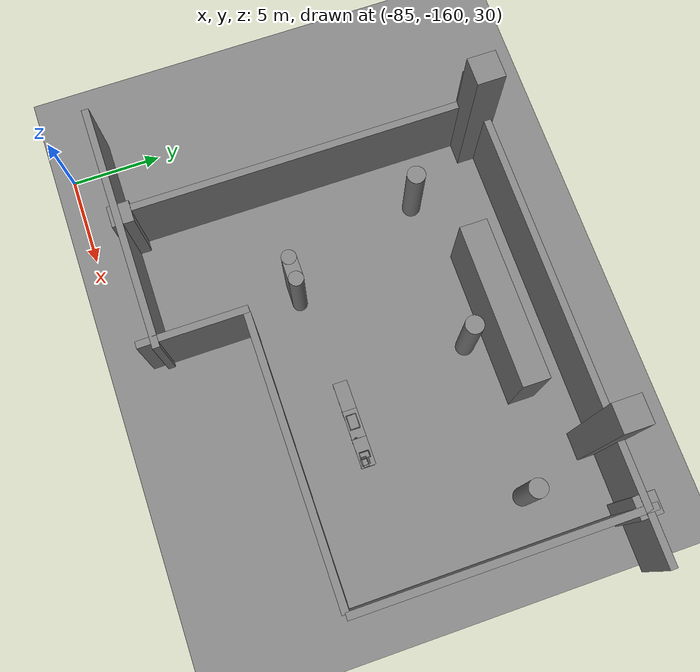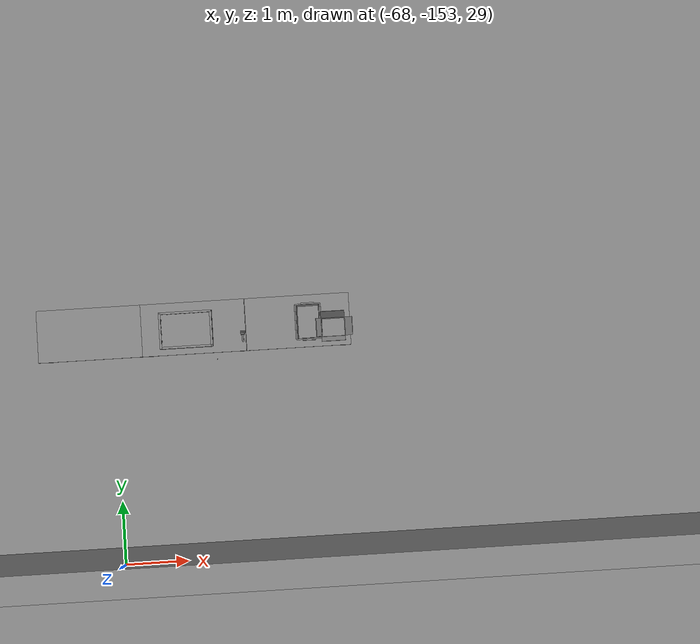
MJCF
<mujoco>
    <option gravity="0.000000000 0.000000000 -9.810000420" timestep="0.0049999999" integrator="implicitfast" density="1.225" viscosity="1.8000001e-05" noslip_iterations="10" iterations="100" sdf_iterations="50">
        <flag multiccd="disable"/>
    </option>
    <size memory="1000M"/>
    <compiler coordinate="local"/>
    <worldbody>
        <light cutoff="30" pos="0 1 1" dir="0 -1 -2"/>
        <light cutoff="30" pos="0 -1 1" dir="0 1 -2"/>
        <body pos="-64.866622925 -149.383972168 30.183746338" euler="89.999992371 89.999946594 0.000000000" name="openloong_gripper_2f85_fix_base_usda_bluebox_01">
            <geom contype="1" conaffinity="1" density="1000" type="box" material="" rgba="0.500000000 0.500000000 0.500000000 1.000000000" solimp="0.899999976 0.949999988 0.001000000" friction="1.000000000 0.005000000 0.000100000" solref="0.020000000 1.000000000" margin="0" condim="3" group="0" pos="0.276596069 0.187225342 0.000061035" quat="0.707107008 0.000077501 0.707106471 0.000077456" size="0.100000001 0.057999998 0.010000000" name="openloong_gripper_2f85_fix_base_usda_geom_A6C64132_B075_424F_89E2_F773B3D35E9E"/>
            <geom contype="1" conaffinity="1" density="1000" type="box" material="" rgba="0.500000000 0.500000000 0.500000000 1.000000000" solimp="0.899999976 0.949999988 0.001000000" friction="1.000000000 0.005000000 0.000100000" solref="0.020000000 1.000000000" margin="0" condim="3" group="0" pos="0.000000000 0.002883911 0.000000000" quat="1.000000000 0.000000000 0.000000000 0.000000000" size="0.254000008 0.003000000 0.172000006" name="openloong_gripper_2f85_fix_base_usda_geom_B21BE933_7A9B_44EA_9661_F88AC2DEC6B2"/>
            <geom contype="1" conaffinity="1" density="1000" type="box" material="" rgba="0.500000000 0.500000000 0.500000000 1.000000000" solimp="0.899999976 0.949999988 0.001000000" friction="1.000000000 0.005000000 0.000100000" solref="0.020000000 1.000000000" margin="0" condim="3" group="0" pos="0.000015259 0.124874115 0.173477173" quat="0.999796450 0.020176515 -0.000000015 0.000000030" size="0.259999990 0.119999997 0.007000000" name="openloong_gripper_2f85_fix_base_usda_geom_B7878323_9F85_4A6E_8508_F292E11ADE84"/>
            <geom contype="1" conaffinity="1" density="1000" type="box" material="" rgba="0.500000000 0.500000000 0.500000000 1.000000000" solimp="0.899999976 0.949999988 0.001000000" friction="1.000000000 0.005000000 0.000100000" solref="0.020000000 1.000000000" margin="0" condim="3" group="0" pos="0.000015259 0.124874115 -0.173477173" quat="0.999796450 -0.020176545 -0.000000015 0.000000000" size="0.259999990 0.119999997 0.007000000" name="openloong_gripper_2f85_fix_base_usda_geom_63D49DDD_F670_41D1_9153_00A807FCBA80"/>
            <geom contype="1" conaffinity="1" density="1000" type="box" material="" rgba="0.500000000 0.500000000 0.500000000 1.000000000" solimp="0.899999976 0.949999988 0.001000000" friction="1.000000000 0.005000000 0.000100000" solref="0.020000000 1.000000000" margin="0" condim="3" group="0" pos="0.000015259 0.214012146 0.188980103" quat="0.999913096 0.013176724 0.000000015 0.000000000" size="0.259999990 0.029999999 0.012500000" name="openloong_gripper_2f85_fix_base_usda_geom_3D37645E_A5D4_447A_B62A_AA960823CFC9"/>
            <geom contype="1" conaffinity="1" density="1000" type="box" material="" rgba="0.500000000 0.500000000 0.500000000 1.000000000" solimp="0.899999976 0.949999988 0.001000000" friction="1.000000000 0.005000000 0.000100000" solref="0.020000000 1.000000000" margin="0" condim="3" group="0" pos="-0.258346558 0.125289917 0.001876831" quat="0.702796996 -0.020792052 0.710783184 0.020769238" size="0.189999998 0.119999997 0.009000000" name="openloong_gripper_2f85_fix_base_usda_geom_C93E2807_140A_4130_B925_4B6B23CD69D9"/>
            <geom contype="1" conaffinity="1" density="1000" type="box" material="" rgba="0.500000000 0.500000000 0.500000000 1.000000000" solimp="0.899999976 0.949999988 0.001000000" friction="1.000000000 0.005000000 0.000100000" solref="0.020000000 1.000000000" margin="0" condim="3" group="0" pos="0.000015259 0.214012146 -0.188980103" quat="0.999913096 -0.013176769 0.000000030 0.000000015" size="0.259999990 0.029999999 0.012500000" name="openloong_gripper_2f85_fix_base_usda_geom_367C2D21_A937_4D4D_BCD7_689E8AB25117"/>
            <geom contype="1" conaffinity="1" density="1000" type="box" material="" rgba="0.500000000 0.500000000 0.500000000 1.000000000" solimp="0.899999976 0.949999988 0.001000000" friction="1.000000000 0.005000000 0.000100000" solref="0.020000000 1.000000000" margin="0" condim="3" group="0" pos="-0.276596069 0.187225342 0.000061035" quat="0.707106650 0.000077441 0.707106709 0.000077456" size="0.100000001 0.057999998 0.010000000" name="openloong_gripper_2f85_fix_base_usda_geom_838EC158_2394_4D43_8419_153962C72E93"/>
            <geom contype="1" conaffinity="1" density="1000" type="box" material="" rgba="0.500000000 0.500000000 0.500000000 1.000000000" solimp="0.899999976 0.949999988 0.001000000" friction="1.000000000 0.005000000 0.000100000" solref="0.020000000 1.000000000" margin="0" condim="3" group="0" pos="0.258346558 0.125289917 0.001876831" quat="0.702851534 0.018856451 0.710823834 -0.019329429" size="0.189999998 0.119999997 0.009000000" name="openloong_gripper_2f85_fix_base_usda_geom_526DD745_FE00_44A9_8055_6108B789C215"/>
            <freejoint name="openloong_gripper_2f85_fix_base_usda_bluebox_01_joint"/>
            <site size="0.005000000 0.005000000 0.005000000" rgba="0.500000000 0.500000000 0.500000000 1.000000000" pos="0.000000000 0.000000000 0.000000000" quat="0.999961913 0.008726534 0.000000000 0.000000000" group="0" type="sphere" name="openloong_gripper_2f85_fix_base_usda_bluebox_01site"/>
        </body>
        <body pos="-64.496299744 -149.491867065 30.235729218" euler="0.000000000 0.000000000 89.999946594" name="openloong_gripper_2f85_fix_base_usda_cardboardbox_01">
            <geom contype="1" conaffinity="1" density="1000" type="box" material="" rgba="0.500000000 0.500000000 0.500000000 1.000000000" solimp="0.899999976 0.949999988 0.001000000" friction="1.000000000 0.005000000 0.000100000" solref="0.020000000 1.000000000" margin="0" condim="3" group="0" pos="-0.003166199 -0.004086494 0.005052090" quat="1.000000000 0.000000000 0.000000000 0.000000000" size="0.142499998 0.177500010 0.005000000" name="openloong_gripper_2f85_fix_base_usda_geom_C1F6B9E2_6867_432F_8132_18E2AC8EFADE"/>
            <geom contype="1" conaffinity="1" density="1000" type="box" material="" rgba="0.500000000 0.500000000 0.500000000 1.000000000" solimp="0.899999976 0.949999988 0.001000000" friction="1.000000000 0.005000000 0.000100000" solref="0.020000000 1.000000000" margin="0" condim="3" group="0" pos="-0.003166199 0.170316696 0.150570869" quat="1.000000000 0.000000000 0.000000000 0.000000000" size="0.142499998 0.005000000 0.149999991" name="openloong_gripper_2f85_fix_base_usda_geom_FED15CC6_86DD_4C26_B6E7_355445205465"/>
            <geom contype="1" conaffinity="1" density="1000" type="box" material="" rgba="0.500000000 0.500000000 0.500000000 1.000000000" solimp="0.899999976 0.949999988 0.001000000" friction="1.000000000 0.005000000 0.000100000" solref="0.020000000 1.000000000" margin="0" condim="3" group="0" pos="-0.147399902 -0.005307198 0.150570869" quat="1.000000000 0.000000000 0.000000000 0.000000000" size="0.005000000 0.177500010 0.149999991" name="openloong_gripper_2f85_fix_base_usda_geom_025A8AF4_5650_4F44_A494_8011B16753C4"/>
            <geom contype="1" conaffinity="1" density="1000" type="box" material="" rgba="0.500000000 0.500000000 0.500000000 1.000000000" solimp="0.899999976 0.949999988 0.001000000" friction="1.000000000 0.005000000 0.000100000" solref="0.020000000 1.000000000" margin="0" condim="3" group="0" pos="0.140275955 -0.005307198 0.150570869" quat="1.000000000 0.000000000 0.000000000 0.000000000" size="0.005000000 0.177500010 0.149999991" name="openloong_gripper_2f85_fix_base_usda_geom_99E8C3CC_8E7F_420F_AC7F_6D408C2B118C"/>
            <geom contype="1" conaffinity="1" density="1000" type="box" material="" rgba="0.500000000 0.500000000 0.500000000 1.000000000" solimp="0.899999976 0.949999988 0.001000000" friction="1.000000000 0.005000000 0.000100000" solref="0.020000000 1.000000000" margin="0" condim="3" group="0" pos="-0.003166199 -0.181550980 0.150570869" quat="1.000000000 0.000000000 0.000000000 0.000000000" size="0.142499998 0.005000000 0.149999991" name="openloong_gripper_2f85_fix_base_usda_geom_14DF023B_E934_4EBE_8BDB_003641570464"/>
            <freejoint name="openloong_gripper_2f85_fix_base_usda_cardboardbox_01_joint"/>
            <site size="0.005000000 0.005000000 0.005000000" rgba="0.500000000 0.500000000 0.500000000 1.000000000" pos="0.000000000 0.000000000 0.000000000" quat="0.999961913 0.008726535 0.000000000 0.000000000" group="0" type="sphere" name="openloong_gripper_2f85_fix_base_usda_site_9A73955E_FC0F_4F4F_9F98_2DA5E1AA4BF0"/>
            <body pos="0.139160156 -0.004048347 0.301930904" euler="-179.999954224 49.383502960 179.999954224" name="openloong_gripper_2f85_fix_base_usda_A1_006">
                <geom contype="1" conaffinity="1" density="1000" type="box" material="" rgba="0.500000000 0.500000000 0.500000000 1.000000000" solimp="0.899999976 0.949999988 0.001000000" friction="1.000000000 0.005000000 0.000100000" solref="0.020000000 1.000000000" margin="0" condim="3" group="0" pos="-0.071587563 0.000009537 0.001745224" quat="0.999999881 0.000000000 0.000000000 0.000000000" size="0.071249999 0.179999992 0.002500000" name="openloong_gripper_2f85_fix_base_usda_geom_33A44560_F712_458E_A8A0_DD6CCB8B1D74"/>
                <joint armature="0" stiffness="0.07" damping="0.0099999998" axis="0.000000 1.000000 0.000000" type="hinge" name="openloong_gripper_2f85_fix_base_usda_A1_006"/>
            </body>
            <body pos="-0.145902634 -0.004086494 0.301938057" euler="-180.000000000 -60.000011444 -180.000000000" name="openloong_gripper_2f85_fix_base_usda_A2_006">
                <geom contype="1" conaffinity="1" density="1000" type="box" material="" rgba="0.500000000 0.500000000 0.500000000 1.000000000" solimp="0.899999976 0.949999988 0.001000000" friction="1.000000000 0.005000000 0.000100000" solref="0.020000000 1.000000000" margin="0" condim="3" group="0" pos="0.071268082 0.000009537 0.002717972" quat="0.000002921 0.000000000 -0.000000030 0.999999881" size="0.071249999 0.179999992 0.002500000" name="openloong_gripper_2f85_fix_base_usda_geom_45F74655_0D90_4E9F_92CD_B659DD0948DE"/>
                <joint armature="0" stiffness="0.07" damping="0.0099999998" axis="0.000000 1.000000 0.000000" type="hinge" name="openloong_gripper_2f85_fix_base_usda_A2_006"/>
            </body>
            <body pos="-0.003385544 0.175991058 0.301930904" euler="-125.858116150 -0.000004561 0.000002331" name="openloong_gripper_2f85_fix_base_usda_B2_006">
                <geom contype="1" conaffinity="1" density="1000" type="box" material="" rgba="0.500000000 0.500000000 0.500000000 1.000000000" solimp="0.899999976 0.949999988 0.001000000" friction="1.000000000 0.005000000 0.000100000" solref="0.020000000 1.000000000" margin="0" condim="3" group="0" pos="0.000009537 -0.070939064 -0.002470016" quat="0.999614120 0.027776197 -0.000000015 0.000000030" size="0.137500003 0.064999998 0.005000000" name="openloong_gripper_2f85_fix_base_usda_geom_13334BA8_B6C3_4667_9C3A_97C949509689"/>
                <joint armature="0" stiffness="0.07" damping="0.0099999998" axis="1.000000 0.000000 0.000000" type="hinge" name="openloong_gripper_2f85_fix_base_usda_B2_006"/>
            </body>
            <body pos="-0.003385544 -0.184140205 0.301938057" euler="147.805557251 0.000000000 0.000000000" name="openloong_gripper_2f85_fix_base_usda_B1_006">
                <geom contype="1" conaffinity="1" density="1000" type="box" material="" rgba="0.500000000 0.500000000 0.500000000 1.000000000" solimp="0.899999976 0.949999988 0.001000000" friction="1.000000000 0.005000000 0.000100000" solref="0.020000000 1.000000000" margin="0" condim="3" group="0" pos="-0.000028610 0.070202351 -0.002703667" quat="0.999614179 -0.027776167 0.000000000 0.000000000" size="0.137500003 0.064999998 0.005000000" name="openloong_gripper_2f85_fix_base_usda_geom_EE3E4151_A434_4600_8880_39A558031B4E"/>
                <joint armature="0" stiffness="0.07" damping="0.0099999998" axis="1.000000 0.000000 0.000000" type="hinge" name="openloong_gripper_2f85_fix_base_usda_B1_006"/>
            </body>
        </body>
        <body pos="-65.882858276 -149.481979370 30.229999542" euler="-64.487716675 0.000000000 0.000000000" name="openloong_gripper_2f85_fix_base_usda_Barcode">
            <geom contype="1" conaffinity="1" density="1000" type="box" material="" rgba="0.500000000 0.500000000 0.500000000 1.000000000" solimp="0.899999976 0.949999988 0.001000000" friction="1.000000000 0.005000000 0.000100000" solref="0.020000000 1.000000000" margin="0" condim="3" group="0" pos="0.000000000 0.013038635 0.001419067" quat="0.000000000 0.000000000 0.000000000 1.000000119" size="0.034000002 0.010000000 0.017999999" name="openloong_gripper_2f85_fix_base_usda_geom_68BFCB0F_57FD_4D06_BE2C_2883654CB0DF"/>
            <geom contype="1" conaffinity="1" density="1000" type="box" material="" rgba="0.500000000 0.500000000 0.500000000 1.000000000" solimp="0.899999976 0.949999988 0.001000000" friction="1.000000000 0.005000000 0.000100000" solref="0.020000000 1.000000000" margin="0" condim="3" group="0" pos="0.000000000 -0.035301208 -0.007095337" quat="0.000000000 0.000000000 -0.043619365 0.999048233" size="0.028999999 0.010000000 0.020000000" name="openloong_gripper_2f85_fix_base_usda_geom_15F068DE_E6E4_494B_9F3B_F8E4ADC22F46"/>
            <geom contype="1" conaffinity="1" density="1000" type="box" material="" rgba="0.500000000 0.500000000 0.500000000 1.000000000" solimp="0.899999976 0.949999988 0.001000000" friction="1.000000000 0.005000000 0.000100000" solref="0.020000000 1.000000000" margin="0" condim="3" group="0" pos="0.000000000 -0.043411255 -0.011749268" quat="0.922262907 0.386563420 0.000000000 0.000000000" size="0.026000001 0.010000000 0.020000000" name="openloong_gripper_2f85_fix_base_usda_geom_FCC9D04D_8E93_499D_B3A8_B8CB1C4F72F5"/>
            <geom contype="1" conaffinity="1" density="1000" type="box" material="" rgba="0.500000000 0.500000000 0.500000000 1.000000000" solimp="0.899999976 0.949999988 0.001000000" friction="1.000000000 0.005000000 0.000100000" solref="0.020000000 1.000000000" margin="0" condim="3" group="0" pos="0.000000000 -0.016967773 -0.031860352" quat="0.000000000 0.000000000 0.000000000 1.000000119" size="0.008000000 0.010000000 0.013000000" name="openloong_gripper_2f85_fix_base_usda_geom_98F91A0A_55AD_413E_9647_B110705CF0D9"/>
            <geom contype="1" conaffinity="1" density="1000" type="box" material="" rgba="0.500000000 0.500000000 0.500000000 1.000000000" solimp="0.899999976 0.949999988 0.001000000" friction="1.000000000 0.005000000 0.000100000" solref="0.020000000 1.000000000" margin="0" condim="3" group="0" pos="0.000000000 -0.001869202 0.000312805" quat="0.953716993 0.300705761 0.000000000 0.000000000" size="0.032000002 0.010000000 0.018999999" name="openloong_gripper_2f85_fix_base_usda_geom_8A22181A_9019_4EB9_8C48_C99BA0CC20F7"/>
            <geom contype="1" conaffinity="1" density="1000" type="box" material="" rgba="0.500000000 0.500000000 0.500000000 1.000000000" solimp="0.899999976 0.949999988 0.001000000" friction="1.000000000 0.005000000 0.000100000" solref="0.020000000 1.000000000" margin="0" condim="3" group="0" pos="0.000000000 -0.019531250 -0.003173828" quat="0.953716993 0.300705761 0.000000000 0.000000000" size="0.030999999 0.010000000 0.020000000" name="openloong_gripper_2f85_fix_base_usda_geom_9C399C30_4C38_4E3A_B785_8EC190248ACD"/>
            <geom contype="1" conaffinity="1" density="1000" type="box" material="" rgba="0.500000000 0.500000000 0.500000000 1.000000000" solimp="0.899999976 0.949999988 0.001000000" friction="1.000000000 0.005000000 0.000100000" solref="0.020000000 1.000000000" margin="0" condim="3" group="0" pos="0.000000000 -0.035301208 -0.007095337" quat="0.953716993 0.300705761 0.000000000 0.000000000" size="0.028999999 0.010000000 0.020000000" name="openloong_gripper_2f85_fix_base_usda_geom_A2FCDDCF_6E7B_429F_B681_0C38079932E3"/>
            <geom contype="1" conaffinity="1" density="1000" type="box" material="" rgba="0.500000000 0.500000000 0.500000000 1.000000000" solimp="0.899999976 0.949999988 0.001000000" friction="1.000000000 0.005000000 0.000100000" solref="0.020000000 1.000000000" margin="0" condim="3" group="0" pos="0.000000000 -0.042617798 -0.071121216" quat="0.000000000 0.000000000 0.000000000 1.000000119" size="0.013000000 0.021000000 0.059999999" name="openloong_gripper_2f85_fix_base_usda_geom_5E866471_04BD_4926_9D49_D18789C0FBA4"/>
            <freejoint name="openloong_gripper_2f85_fix_base_usda_Barcode_joint"/>
            <site size="0.005000000 0.005000000 0.005000000" rgba="0.500000000 0.500000000 0.500000000 1.000000000" pos="0.000000000 0.000000000 0.000000000" quat="1.000000000 0.000000000 0.000000000 0.000000000" group="0" type="sphere" name="openloong_gripper_2f85_fix_base_usda_Barcode_site"/>
        </body>
        <body pos="-66.745018005 -149.392349243 30.184000015" euler="0.000000000 0.000000000 89.999946594" name="[22332007966145]_Basket_01">
            <geom contype="1" conaffinity="1" density="1000" type="box" material="" rgba="0.500000000 0.500000000 0.500000000 1.000000000" solimp="0.899999976 0.949999988 0.001000000" friction="1.000000000 0.005000000 0.000100000" solref="0.020000000 1.000000000" margin="0" condim="3" group="0" pos="-0.052425385 0.389207840 0.089787483" quat="0.707107008 0.000000000 0.000000000 0.707106411" size="0.014249999 0.014249999 0.059999999" name="[22332007966145]_geom_54C4E61D_AC42_4025_9A0D_D76D906E04FC"/>
            <geom contype="1" conaffinity="1" density="1000" type="box" material="" rgba="0.500000000 0.500000000 0.500000000 1.000000000" solimp="0.899999976 0.949999988 0.001000000" friction="1.000000000 0.005000000 0.000100000" solref="0.020000000 1.000000000" margin="0" condim="3" group="0" pos="0.264015198 -0.133043289 0.089787483" quat="0.707107008 0.000000000 0.000000000 0.707106411" size="0.014249999 0.014249999 0.059999999" name="[22332007966145]_geom_58A77333_2453_4461_A02F_4F5016EA637F"/>
            <geom contype="1" conaffinity="1" density="1000" type="box" material="" rgba="0.500000000 0.500000000 0.500000000 1.000000000" solimp="0.899999976 0.949999988 0.001000000" friction="1.000000000 0.005000000 0.000100000" solref="0.020000000 1.000000000" margin="0" condim="3" group="0" pos="-0.264015198 -0.265548706 0.089793205" quat="0.707107008 0.000000000 0.000000000 0.707106411" size="0.014249999 0.014249999 0.059999999" name="[22332007966145]_geom_E6B1033C_65B1_46C0_AD00_1DF0A88BBEA2"/>
            <geom contype="1" conaffinity="1" density="1000" type="box" material="" rgba="0.500000000 0.500000000 0.500000000 1.000000000" solimp="0.899999976 0.949999988 0.001000000" friction="1.000000000 0.005000000 0.000100000" solref="0.020000000 1.000000000" margin="0" condim="3" group="0" pos="-0.160263062 -0.389322281 0.089793205" quat="0.707107008 0.000000000 0.000000000 0.707106411" size="0.014249999 0.014249999 0.059999999" name="[22332007966145]_geom_1CF22201_9C9F_404E_A68D_DB0AAB5C453E"/>
            <geom contype="1" conaffinity="1" density="1000" type="box" material="" rgba="0.500000000 0.500000000 0.500000000 1.000000000" solimp="0.899999976 0.949999988 0.001000000" friction="1.000000000 0.005000000 0.000100000" solref="0.020000000 1.000000000" margin="0" condim="3" group="0" pos="0.162265778 -0.389322281 0.089787483" quat="0.707107008 0.000000000 0.000000000 0.707106411" size="0.014249999 0.014249999 0.059999999" name="[22332007966145]_geom_EF061EF7_7150_4954_AC17_AF3DBAD1AE85"/>
            <geom contype="1" conaffinity="1" density="1000" type="box" material="" rgba="0.500000000 0.500000000 0.500000000 1.000000000" solimp="0.899999976 0.949999988 0.001000000" friction="1.000000000 0.005000000 0.000100000" solref="0.020000000 1.000000000" margin="0" condim="3" group="0" pos="0.264015198 0.389207840 0.089787483" quat="0.707107008 0.000000000 0.000000000 0.707106411" size="0.014249999 0.014249999 0.059999999" name="[22332007966145]_geom_F1157AEE_05E1_474E_A5C1_F4FA750AEAD6"/>
            <geom contype="1" conaffinity="1" density="1000" type="box" material="" rgba="0.500000000 0.500000000 0.500000000 1.000000000" solimp="0.899999976 0.949999988 0.001000000" friction="1.000000000 0.005000000 0.000100000" solref="0.020000000 1.000000000" margin="0" condim="3" group="0" pos="-0.264015198 -0.133043289 0.089793205" quat="0.707107008 0.000000000 0.000000000 0.707106411" size="0.014249999 0.014249999 0.059999999" name="[22332007966145]_geom_C038D0FE_E658_4C51_9384_4178DA4AD86D"/>
            <geom contype="1" conaffinity="1" density="1000" type="box" material="" rgba="0.500000000 0.500000000 0.500000000 1.000000000" solimp="0.899999976 0.949999988 0.001000000" friction="1.000000000 0.005000000 0.000100000" solref="0.020000000 1.000000000" margin="0" condim="3" group="0" pos="-0.264026642 0.269256592 0.089793205" quat="0.707107008 0.000000000 0.000000000 0.707106411" size="0.014249999 0.014249999 0.059999999" name="[22332007966145]_geom_57807DDF_9193_49C6_AF32_383B175D1760"/>
            <geom contype="1" conaffinity="1" density="1000" type="box" material="" rgba="0.500000000 0.500000000 0.500000000 1.000000000" solimp="0.899999976 0.949999988 0.001000000" friction="1.000000000 0.005000000 0.000100000" solref="0.020000000 1.000000000" margin="0" condim="3" group="0" pos="0.054462433 0.389207840 0.089787483" quat="0.707107008 0.000000000 0.000000000 0.707106411" size="0.014249999 0.014249999 0.059999999" name="[22332007966145]_geom_4E7D8D58_5B81_4EDE_863A_23AE9BB3F990"/>
            <geom contype="1" conaffinity="1" density="1000" type="box" material="" rgba="0.500000000 0.500000000 0.500000000 1.000000000" solimp="0.899999976 0.949999988 0.001000000" friction="1.000000000 0.005000000 0.000100000" solref="0.020000000 1.000000000" margin="0" condim="3" group="0" pos="0.054462433 -0.389322281 0.089787483" quat="0.707107008 0.000000000 0.000000000 0.707106411" size="0.014249999 0.014249999 0.059999999" name="[22332007966145]_geom_2734B66B_304D_4129_AC15_A21F9C23925C"/>
            <geom contype="1" conaffinity="1" density="1000" type="box" material="" rgba="0.500000000 0.500000000 0.500000000 1.000000000" solimp="0.899999976 0.949999988 0.001000000" friction="1.000000000 0.005000000 0.000100000" solref="0.020000000 1.000000000" margin="0" condim="3" group="0" pos="0.264015198 0.269256592 0.089793205" quat="0.707107008 0.000000000 0.000000000 0.707106411" size="0.014249999 0.014249999 0.059999999" name="[22332007966145]_geom_4761A7F0_943A_4D90_9FDA_55AC57CFE61D"/>
            <geom contype="1" conaffinity="1" density="1000" type="box" material="" rgba="0.500000000 0.500000000 0.500000000 1.000000000" solimp="0.899999976 0.949999988 0.001000000" friction="1.000000000 0.005000000 0.000100000" solref="0.020000000 1.000000000" margin="0" condim="3" group="0" pos="0.264015198 -0.389322281 0.089787483" quat="0.707107008 0.000000000 0.000000000 0.707106411" size="0.014249999 0.014249999 0.059999999" name="[22332007966145]_geom_C61D0335_35F1_4A75_9114_EFD3293A9B6E"/>
            <geom contype="1" conaffinity="1" density="1000" type="box" material="" rgba="0.500000000 0.500000000 0.500000000 1.000000000" solimp="0.899999976 0.949999988 0.001000000" friction="1.000000000 0.005000000 0.000100000" solref="0.020000000 1.000000000" margin="0" condim="3" group="0" pos="0.000000000 0.000000000 0.015998840" quat="0.707107008 0.000000000 0.000000000 0.707106411" size="0.403499991 0.279000014 0.015750000" name="[22332007966145]_geom_178DE838_C933_4122_96CD_AB0436690FE5"/>
            <geom contype="1" conaffinity="1" density="1000" type="box" material="" rgba="0.500000000 0.500000000 0.500000000 1.000000000" solimp="0.899999976 0.949999988 0.001000000" friction="1.000000000 0.005000000 0.000100000" solref="0.020000000 1.000000000" margin="0" condim="3" group="0" pos="0.000000000 -0.389476776 0.163619041" quat="0.707107008 0.000000000 0.000000000 0.707106411" size="0.015000000 0.277500004 0.015750000" name="[22332007966145]_geom_DE4CB675_D91F_46A3_BAD6_1411D2E7FE2A"/>
            <geom contype="1" conaffinity="1" density="1000" type="box" material="" rgba="0.500000000 0.500000000 0.500000000 1.000000000" solimp="0.899999976 0.949999988 0.001000000" friction="1.000000000 0.005000000 0.000100000" solref="0.020000000 1.000000000" margin="0" condim="3" group="0" pos="0.162265778 0.389207840 0.089787483" quat="0.707107008 0.000000000 0.000000000 0.707106411" size="0.014249999 0.014249999 0.059999999" name="[22332007966145]_geom_C82451FB_FDDE_4117_8553_A11C6225EEA6"/>
            <geom contype="1" conaffinity="1" density="1000" type="box" material="" rgba="0.500000000 0.500000000 0.500000000 1.000000000" solimp="0.899999976 0.949999988 0.001000000" friction="1.000000000 0.005000000 0.000100000" solref="0.020000000 1.000000000" margin="0" condim="3" group="0" pos="0.000000000 0.389471054 0.163619041" quat="0.707107008 0.000000000 0.000000000 0.707106411" size="0.015000000 0.277500004 0.015750000" name="[22332007966145]_geom_04FD23B7_A14D_4E35_986F_33CF373F34AF"/>
            <geom contype="1" conaffinity="1" density="1000" type="box" material="" rgba="0.500000000 0.500000000 0.500000000 1.000000000" solimp="0.899999976 0.949999988 0.001000000" friction="1.000000000 0.005000000 0.000100000" solref="0.020000000 1.000000000" margin="0" condim="3" group="0" pos="-0.263511658 0.000000000 0.163619041" quat="0.707107008 0.000000000 0.000000000 0.707106411" size="0.403499991 0.015000000 0.015750000" name="[22332007966145]_geom_1DECB408_AF64_4050_AF25_BC8ACF60D38D"/>
            <geom contype="1" conaffinity="1" density="1000" type="box" material="" rgba="0.500000000 0.500000000 0.500000000 1.000000000" solimp="0.899999976 0.949999988 0.001000000" friction="1.000000000 0.005000000 0.000100000" solref="0.020000000 1.000000000" margin="0" condim="3" group="0" pos="-0.264015198 0.141334534 0.089793205" quat="0.707107008 0.000000000 0.000000000 0.707106411" size="0.014249999 0.014249999 0.059999999" name="[22332007966145]_geom_034142CB_2422_4ED9_91C2_C3C71A831D0B"/>
            <geom contype="1" conaffinity="1" density="1000" type="box" material="" rgba="0.500000000 0.500000000 0.500000000 1.000000000" solimp="0.899999976 0.949999988 0.001000000" friction="1.000000000 0.005000000 0.000100000" solref="0.020000000 1.000000000" margin="0" condim="3" group="0" pos="0.264015198 -0.265548706 0.089787483" quat="0.707107008 0.000000000 0.000000000 0.707106411" size="0.014249999 0.014249999 0.059999999" name="[22332007966145]_geom_C5196400_F38D_41F2_8855_1965272D7DE4"/>
            <geom contype="1" conaffinity="1" density="1000" type="box" material="" rgba="0.500000000 0.500000000 0.500000000 1.000000000" solimp="0.899999976 0.949999988 0.001000000" friction="1.000000000 0.005000000 0.000100000" solref="0.020000000 1.000000000" margin="0" condim="3" group="0" pos="-0.160263062 0.389207840 0.089787483" quat="0.707107008 0.000000000 0.000000000 0.707106411" size="0.014249999 0.014249999 0.059999999" name="[22332007966145]_geom_A750D226_8150_45E4_AB2A_84942905C677"/>
            <geom contype="1" conaffinity="1" density="1000" type="box" material="" rgba="0.500000000 0.500000000 0.500000000 1.000000000" solimp="0.899999976 0.949999988 0.001000000" friction="1.000000000 0.005000000 0.000100000" solref="0.020000000 1.000000000" margin="0" condim="3" group="0" pos="-0.052425385 -0.389322281 0.089787483" quat="0.707107008 0.000000000 0.000000000 0.707106411" size="0.014249999 0.014249999 0.059999999" name="[22332007966145]_geom_4F0FC569_E011_498E_B80A_43ED9514C70A"/>
            <geom contype="1" conaffinity="1" density="1000" type="box" material="" rgba="0.500000000 0.500000000 0.500000000 1.000000000" solimp="0.899999976 0.949999988 0.001000000" friction="1.000000000 0.005000000 0.000100000" solref="0.020000000 1.000000000" margin="0" condim="3" group="0" pos="-0.264026642 -0.389322281 0.089793205" quat="0.707107008 0.000000000 0.000000000 0.707106411" size="0.014249999 0.014249999 0.059999999" name="[22332007966145]_geom_17CB7C65_1F32_435A_A369_026526FF338C"/>
            <geom contype="1" conaffinity="1" density="1000" type="box" material="" rgba="0.500000000 0.500000000 0.500000000 1.000000000" solimp="0.899999976 0.949999988 0.001000000" friction="1.000000000 0.005000000 0.000100000" solref="0.020000000 1.000000000" margin="0" condim="3" group="0" pos="0.264015198 0.141334534 0.089787483" quat="0.707107008 0.000000000 0.000000000 0.707106411" size="0.014249999 0.014249999 0.059999999" name="[22332007966145]_geom_59344805_E500_45DA_B8FE_87D0EFA47B08"/>
            <geom contype="1" conaffinity="1" density="1000" type="box" material="" rgba="0.500000000 0.500000000 0.500000000 1.000000000" solimp="0.899999976 0.949999988 0.001000000" friction="1.000000000 0.005000000 0.000100000" solref="0.020000000 1.000000000" margin="0" condim="3" group="0" pos="-0.264015198 0.389207840 0.089793205" quat="0.707107008 0.000000000 0.000000000 0.707106411" size="0.014249999 0.014249999 0.059999999" name="[22332007966145]_geom_5E1B92BD_FD47_4272_BD39_7BA93D0A6BE7"/>
            <geom contype="1" conaffinity="1" density="1000" type="box" material="" rgba="0.500000000 0.500000000 0.500000000 1.000000000" solimp="0.899999976 0.949999988 0.001000000" friction="1.000000000 0.005000000 0.000100000" solref="0.020000000 1.000000000" margin="0" condim="3" group="0" pos="0.264015198 0.004480362 0.089787483" quat="0.707107008 0.000000000 0.000000000 0.707106411" size="0.014249999 0.014249999 0.059999999" name="[22332007966145]_geom_844CAB11_7398_4473_A100_5D6B9E968DDF"/>
            <geom contype="1" conaffinity="1" density="1000" type="box" material="" rgba="0.500000000 0.500000000 0.500000000 1.000000000" solimp="0.899999976 0.949999988 0.001000000" friction="1.000000000 0.005000000 0.000100000" solref="0.020000000 1.000000000" margin="0" condim="3" group="0" pos="0.263694763 -0.000011444 0.163619041" quat="0.707107008 0.000000000 0.000000000 0.707106411" size="0.403499991 0.015000000 0.015750000" name="[22332007966145]_geom_D83951C7_E26B_4C82_BDF4_CB80943F4D97"/>
            <geom contype="1" conaffinity="1" density="1000" type="box" material="" rgba="0.500000000 0.500000000 0.500000000 1.000000000" solimp="0.899999976 0.949999988 0.001000000" friction="1.000000000 0.005000000 0.000100000" solref="0.020000000 1.000000000" margin="0" condim="3" group="0" pos="-0.264015198 0.004480362 0.089793205" quat="0.707107008 0.000000000 0.000000000 0.707106411" size="0.014249999 0.014249999 0.059999999" name="[22332007966145]_geom_622B05F8_E900_44C4_B8FB_5591C447665B"/>
            <freejoint name="[22332007966145]_joint_E662A2A8_D856_4F04_8D41_6CBFC53108FB"/>
        </body>
        <body pos="0.000000000 0.000000000 0.000000000" euler="0.000000000 0.000000000 0.000000000" name="Static Objects_Static Objects">
            <geom contype="1" conaffinity="1" density="1000" type="box" material="" rgba="0.500000000 0.500000000 0.500000000 1.000000000" solimp="0.899999976 0.949999988 0.001000000" friction="1.000000000 0.005000000 0.000100000" solref="0.020000000 1.000000000" margin="0" condim="3" group="0" pos="-67.544113159 -149.365814209 29.727830887" quat="0.500000417 0.499999970 0.499999553 0.499999970" size="0.381000012 0.319999993 0.041000001" name="Static Objects_geom_3E215E9B_F24D_49B1_A8DA_B9E171861BE0"/>
            <geom contype="1" conaffinity="1" density="1000" type="box" material="" rgba="0.500000000 0.500000000 0.500000000 1.000000000" solimp="0.899999976 0.949999988 0.001000000" friction="1.000000000 0.005000000 0.000100000" solref="0.020000000 1.000000000" margin="0" condim="3" group="0" pos="-68.239501953 -149.365814209 30.086868286" quat="0.500000417 0.499999970 0.499999553 0.499999970" size="0.370999992 0.039500002 0.745000005" name="Static Objects_geom_CC2B50C7_5CE7_405B_A65F_2772D312EF6C"/>
            <geom contype="1" conaffinity="1" density="1000" type="box" material="" rgba="0.500000000 0.500000000 0.500000000 1.000000000" solimp="0.899999976 0.949999988 0.001000000" friction="1.000000000 0.005000000 0.000100000" solref="0.020000000 1.000000000" margin="0" condim="3" group="0" pos="-68.239501953 -149.365814209 30.147235870" quat="0.500000417 0.499999970 0.499999553 0.499999970" size="0.400000006 0.022000000 0.800000012" name="Static Objects_geom_C422263F_7C29_4777_A1E9_D9E765C0FF53"/>
            <geom contype="1" conaffinity="1" density="1000" type="box" material="" rgba="0.500000000 0.500000000 0.500000000 1.000000000" solimp="0.899999976 0.949999988 0.001000000" friction="1.000000000 0.005000000 0.000100000" solref="0.020000000 1.000000000" margin="0" condim="3" group="0" pos="-68.934890747 -149.365814209 29.727830887" quat="0.500000417 0.499999970 0.499999553 0.499999970" size="0.381000012 0.319999993 0.041000001" name="Static Objects_geom_6365B512_3129_40C1_ADCC_4B750A9C6BC8"/>
            <geom contype="1" conaffinity="1" density="1000" type="box" material="" rgba="0.500000000 0.500000000 0.500000000 1.000000000" solimp="0.899999976 0.949999988 0.001000000" friction="1.000000000 0.005000000 0.000100000" solref="0.020000000 1.000000000" margin="0" condim="3" group="0" pos="-68.239501953 -149.365814209 29.561563492" quat="0.500000417 0.499999970 0.499999553 0.499999970" size="0.020000000 0.022000000 0.660000026" name="Static Objects_geom_18B34DE9_0812_48AE_8BC6_7B4E2C7E7266"/>
            <geom contype="1" conaffinity="1" density="1000" type="box" material="" rgba="0.500000000 0.500000000 0.500000000 1.000000000" solimp="0.899999976 0.949999988 0.001000000" friction="1.000000000 0.005000000 0.000100000" solref="0.020000000 1.000000000" margin="0" condim="3" group="0" pos="-65.945671082 -149.365814209 29.727830887" quat="0.500000417 0.499999970 0.499999553 0.499999970" size="0.381000012 0.319999993 0.041000001" name="Static Objects_geom_23E26A36_CF90_48EE_9434_2BE12E699AC9"/>
            <geom contype="1" conaffinity="1" density="1000" type="box" material="" rgba="0.500000000 0.500000000 0.500000000 1.000000000" solimp="0.899999976 0.949999988 0.001000000" friction="1.000000000 0.005000000 0.000100000" solref="0.020000000 1.000000000" margin="0" condim="3" group="0" pos="-66.641059875 -149.365814209 30.086868286" quat="0.500000417 0.499999970 0.499999553 0.499999970" size="0.370999992 0.039500002 0.745000005" name="Static Objects_geom_F5FAD72E_A6BA_40E9_A68D_3E7E86DA5A91"/>
            <geom contype="1" conaffinity="1" density="1000" type="box" material="" rgba="0.500000000 0.500000000 0.500000000 1.000000000" solimp="0.899999976 0.949999988 0.001000000" friction="1.000000000 0.005000000 0.000100000" solref="0.020000000 1.000000000" margin="0" condim="3" group="0" pos="-66.641059875 -149.365814209 30.147235870" quat="0.500000417 0.499999970 0.499999553 0.499999970" size="0.400000006 0.022000000 0.800000012" name="Static Objects_geom_50CC54DC_FC45_403E_B571_75F504FE278F"/>
            <geom contype="1" conaffinity="1" density="1000" type="box" material="" rgba="0.500000000 0.500000000 0.500000000 1.000000000" solimp="0.899999976 0.949999988 0.001000000" friction="1.000000000 0.005000000 0.000100000" solref="0.020000000 1.000000000" margin="0" condim="3" group="0" pos="-67.336448669 -149.365814209 29.727830887" quat="0.500000417 0.499999970 0.499999553 0.499999970" size="0.381000012 0.319999993 0.041000001" name="Static Objects_geom_97F6157B_1A7D_4470_9EED_DBC2E15BBF9E"/>
            <geom contype="1" conaffinity="1" density="1000" type="box" material="" rgba="0.500000000 0.500000000 0.500000000 1.000000000" solimp="0.899999976 0.949999988 0.001000000" friction="1.000000000 0.005000000 0.000100000" solref="0.020000000 1.000000000" margin="0" condim="3" group="0" pos="-66.641059875 -149.365814209 29.561563492" quat="0.500000417 0.499999970 0.499999553 0.499999970" size="0.020000000 0.022000000 0.660000026" name="Static Objects_geom_BFF2658B_ABED_421A_BE90_FCFE5DBF2753"/>
            <geom contype="1" conaffinity="1" density="1000" type="box" material="" rgba="0.500000000 0.500000000 0.500000000 1.000000000" solimp="0.899999976 0.949999988 0.001000000" friction="1.000000000 0.005000000 0.000100000" solref="0.020000000 1.000000000" margin="0" condim="3" group="0" pos="-64.338577271 -149.365814209 29.727830887" quat="0.500000417 0.499999970 0.499999553 0.499999970" size="0.381000012 0.319999993 0.041000001" name="Static Objects_geom_F3343077_F432_4B80_BC63_D411E89EF69F"/>
            <geom contype="1" conaffinity="1" density="1000" type="box" material="" rgba="0.500000000 0.500000000 0.500000000 1.000000000" solimp="0.899999976 0.949999988 0.001000000" friction="1.000000000 0.005000000 0.000100000" solref="0.020000000 1.000000000" margin="0" condim="3" group="0" pos="-65.033966064 -149.365814209 30.086868286" quat="0.500000417 0.499999970 0.499999553 0.499999970" size="0.370999992 0.039500002 0.745000005" name="Static Objects_geom_3E2B9AC0_90C9_4E0F_952A_79E289C19BB6"/>
            <geom contype="1" conaffinity="1" density="1000" type="box" material="" rgba="0.500000000 0.500000000 0.500000000 1.000000000" solimp="0.899999976 0.949999988 0.001000000" friction="1.000000000 0.005000000 0.000100000" solref="0.020000000 1.000000000" margin="0" condim="3" group="0" pos="-65.033966064 -149.365814209 30.147235870" quat="0.500000417 0.499999970 0.499999553 0.499999970" size="0.400000006 0.022000000 0.800000012" name="Static Objects_geom_77D89C38_508D_429F_AD40_3B74A5AB5365"/>
            <geom contype="1" conaffinity="1" density="1000" type="box" material="" rgba="0.500000000 0.500000000 0.500000000 1.000000000" solimp="0.899999976 0.949999988 0.001000000" friction="1.000000000 0.005000000 0.000100000" solref="0.020000000 1.000000000" margin="0" condim="3" group="0" pos="-65.729354858 -149.365814209 29.727830887" quat="0.500000417 0.499999970 0.499999553 0.499999970" size="0.381000012 0.319999993 0.041000001" name="Static Objects_geom_E9DE1C74_EE6A_47AE_B1F8_26A28157BCF3"/>
            <geom contype="1" conaffinity="1" density="1000" type="box" material="" rgba="0.500000000 0.500000000 0.500000000 1.000000000" solimp="0.899999976 0.949999988 0.001000000" friction="1.000000000 0.005000000 0.000100000" solref="0.020000000 1.000000000" margin="0" condim="3" group="0" pos="-65.033966064 -149.365814209 29.561563492" quat="0.500000417 0.499999970 0.499999553 0.499999970" size="0.020000000 0.022000000 0.660000026" name="Static Objects_geom_6123470E_6F02_43A0_8EFE_E9AD82AC4AD2"/>
            <geom contype="1" conaffinity="1" density="1000" type="box" material="" rgba="0.500000000 0.500000000 0.500000000 1.000000000" solimp="0.899999976 0.949999988 0.001000000" friction="1.000000000 0.005000000 0.000100000" solref="0.020000000 1.000000000" margin="0" condim="3" group="0" pos="-61.754566193 -137.853729248 33.906845093" quat="0.707107067 0.000000000 0.000000000 0.707106471" size="0.759999990 0.759999990 4.500000000" name="Static Objects_geom_662AE0DF_0219_4D7B_B2FF_AAD9633FDC95"/>
            <geom contype="1" conaffinity="1" density="1000" type="box" material="" rgba="0.500000000 0.500000000 0.500000000 1.000000000" solimp="0.899999976 0.949999988 0.001000000" friction="1.000000000 0.005000000 0.000100000" solref="0.020000000 1.000000000" margin="0" condim="3" group="0" pos="-57.511135101 -144.927108765 31.707921982" quat="1.000000000 0.000000000 0.000000000 0.000000000" size="0.200000003 8.000000000 2.299999952" name="Static Objects_geom_3B114340_56B3_465A_9AFA_0136E3F4F3F7"/>
            <geom contype="1" conaffinity="1" density="1000" type="box" material="" rgba="0.500000000 0.500000000 0.500000000 1.000000000" solimp="0.899999976 0.949999988 0.001000000" friction="1.000000000 0.005000000 0.000100000" solref="0.020000000 1.000000000" margin="0" condim="3" group="0" pos="-80.517646790 -157.574050903 31.688196182" quat="0.707107067 0.000000000 0.000000000 0.707106471" size="0.600000024 0.600000024 2.299999952" name="Static Objects_geom_72206714_453F_48A7_B551_500DC066D1EE"/>
            <geom contype="1" conaffinity="1" density="1000" type="box" material="" rgba="0.500000000 0.500000000 0.500000000 1.000000000" solimp="0.899999976 0.949999988 0.001000000" friction="1.000000000 0.005000000 0.000100000" solref="0.020000000 1.000000000" margin="0" condim="3" group="0" pos="-80.711044312 -147.414932251 31.666158676" quat="1.000000000 0.000000000 0.000000000 0.000000000" size="0.200000003 10.000000000 2.299999952" name="Static Objects_geom_553D9329_461D_49B5_B399_BACF9F698D93"/>
            <geom contype="1" conaffinity="1" density="1000" type="box" material="" rgba="0.500000000 0.500000000 0.500000000 1.000000000" solimp="0.899999976 0.949999988 0.001000000" friction="1.000000000 0.005000000 0.000100000" solref="0.020000000 1.000000000" margin="0" condim="3" group="0" pos="-57.687217712 -137.434692383 31.688196182" quat="0.707107067 0.000000000 0.000000000 0.707106471" size="0.600000024 0.600000024 2.299999952" name="Static Objects_geom_3DE6282A_4389_4FA8_91DA_AF639DC5F49F"/>
            <geom contype="1" conaffinity="1" density="1000" type="box" material="" rgba="0.500000000 0.500000000 0.500000000 1.000000000" solimp="0.899999976 0.949999988 0.001000000" friction="1.000000000 0.005000000 0.000100000" solref="0.020000000 1.000000000" margin="0" condim="3" group="0" pos="-69.537033081 -140.263229370 31.714921951" quat="0.707107067 0.000000000 0.000000000 0.707106471" size="0.759999990 4.500000000 2.299999952" name="Static Objects_geom_2A331F9B_89A8_444B_9FB9_4E577204B3D5"/>
            <geom contype="1" conaffinity="1" density="1000" type="box" material="" rgba="0.500000000 0.500000000 0.500000000 1.000000000" solimp="0.899999976 0.949999988 0.001000000" friction="1.000000000 0.005000000 0.000100000" solref="0.020000000 1.000000000" margin="0" condim="3" group="0" pos="-80.073638916 -137.853713989 33.906845093" quat="0.707107067 0.000000000 0.000000000 0.707106471" size="0.759999990 0.759999990 4.500000000" name="Static Objects_geom_F17EEE17_05BE_47B4_B2A5_25D4B4F3F399"/>
            <geom contype="1" conaffinity="1" density="1000" type="box" material="" rgba="0.500000000 0.500000000 0.500000000 1.000000000" solimp="0.899999976 0.949999988 0.001000000" friction="1.000000000 0.005000000 0.000100000" solref="0.020000000 1.000000000" margin="0" condim="3" group="0" pos="-73.406707764 -155.734664917 31.707921982" quat="1.000000000 0.000000000 0.000000000 0.000000000" size="0.200000003 3.000000000 2.299999952" name="Static Objects_geom_1F55FECD_3AD4_41EA_AE3E_7FE517E126FA"/>
            <geom contype="1" conaffinity="1" density="1000" type="box" material="" rgba="0.500000000 0.500000000 0.500000000 1.000000000" solimp="0.899999976 0.949999988 0.001000000" friction="1.000000000 0.005000000 0.000100000" solref="0.020000000 1.000000000" margin="0" condim="3" group="0" pos="-68.497543335 -137.448257446 31.707921982" quat="0.707107067 0.000000000 0.000000000 0.707106471" size="0.200000003 14.000000000 2.299999952" name="Static Objects_geom_99029FE1_B1D1_4F40_B053_03FC892B5A85"/>
            <geom contype="1" conaffinity="1" density="1000" type="cylinder" material="" rgba="0.500000000 0.500000000 0.500000000 1.000000000" solimp="0.899999976 0.949999988 0.001000000" friction="1.000000000 0.005000000 0.000100000" solref="0.020000000 1.000000000" margin="0" condim="3" group="0" pos="-68.868522644 -142.134506226 31.711090088" quat="0.707107067 0.000000000 0.000000000 0.707106471" size="0.509999990 2.299999952 1.000000000" name="Static Objects_geom_C7FDAF00_D893_44DF_9322_EA43C5430941"/>
            <geom contype="1" conaffinity="1" density="1000" type="plane" material="" rgba="0.500000000 0.500000000 0.500000000 1.000000000" solimp="0.899999976 0.949999988 0.001000000" friction="1.000000000 0.005000000 0.000100000" solref="0.020000000 1.000000000" margin="0" condim="3" group="0" pos="-72.873703003 -147.131927490 29.409669876" quat="1.000000000 0.000000000 0.000000000 0.000000000" size="18.000000000 14.000000000 1.000000000" name="Static Objects_geom_20F479BE_5D19_4982_8221_FDC8B6855B2F"/>
            <geom contype="1" conaffinity="1" density="1000" type="box" material="" rgba="0.500000000 0.500000000 0.500000000 1.000000000" solimp="0.899999976 0.949999988 0.001000000" friction="1.000000000 0.005000000 0.000100000" solref="0.020000000 1.000000000" margin="0" condim="3" group="0" pos="-79.943580627 -157.782272339 31.707921982" quat="0.707107067 0.000000000 0.000000000 0.707106471" size="0.200000003 7.000000000 2.299999952" name="Static Objects_geom_371BBC5A_E4EA_47C1_9D33_4F4F0EF08A3B"/>
            <geom contype="1" conaffinity="1" density="1000" type="box" material="" rgba="0.500000000 0.500000000 0.500000000 1.000000000" solimp="0.899999976 0.949999988 0.001000000" friction="1.000000000 0.005000000 0.000100000" solref="0.020000000 1.000000000" margin="0" condim="3" group="0" pos="-65.421028137 -152.903442383 31.707921982" quat="0.707107067 0.000000000 0.000000000 0.707106471" size="0.200000003 7.800000191 2.299999952" name="Static Objects_geom_FA89298C_5085_49F5_9295_CB6BFE695317"/>
            <geom contype="1" conaffinity="1" density="1000" type="box" material="" rgba="0.500000000 0.500000000 0.500000000 1.000000000" solimp="0.899999976 0.949999988 0.001000000" friction="1.000000000 0.005000000 0.000100000" solref="0.020000000 1.000000000" margin="0" condim="3" group="0" pos="-74.776908875 -149.964416504 31.688196182" quat="1.000000000 0.000000000 0.000000000 0.000000000" size="0.600000024 0.409999996 2.299999952" name="Static Objects_geom_B7549B15_1595_4E62_B737_CA84E6ABF8D6"/>
            <geom contype="1" conaffinity="1" density="1000" type="cylinder" material="" rgba="0.500000000 0.500000000 0.500000000 1.000000000" solimp="0.899999976 0.949999988 0.001000000" friction="1.000000000 0.005000000 0.000100000" solref="0.020000000 1.000000000" margin="0" condim="3" group="0" pos="-60.161884308 -142.134506226 31.711090088" quat="0.707107067 0.000000000 0.000000000 0.707106471" size="0.509999990 2.299999952 1.000000000" name="Static Objects_geom_BCE61857_989C_402D_B7D3_97C56DDF931A"/>
            <geom contype="1" conaffinity="1" density="1000" type="cylinder" material="" rgba="0.500000000 0.500000000 0.500000000 1.000000000" solimp="0.899999976 0.949999988 0.001000000" friction="1.000000000 0.005000000 0.000100000" solref="0.020000000 1.000000000" margin="0" condim="3" group="0" pos="-75.382453918 -149.963455200 31.711090088" quat="0.707107067 0.000000000 0.000000000 0.707106471" size="0.409999996 2.299999952 1.000000000" name="Static Objects_geom_ADE64212_D947_4AE5_8561_75F1B4845E88"/>
            <geom contype="1" conaffinity="1" density="1000" type="cylinder" material="" rgba="0.500000000 0.500000000 0.500000000 1.000000000" solimp="0.899999976 0.949999988 0.001000000" friction="1.000000000 0.005000000 0.000100000" solref="0.020000000 1.000000000" margin="0" condim="3" group="0" pos="-74.154960632 -149.963455200 31.711090088" quat="0.707107067 0.000000000 0.000000000 0.707106471" size="0.409999996 2.299999952 1.000000000" name="Static Objects_geom_A823AFAE_6740_4B39_B8B5_4B3F2D152A20"/>
            <geom contype="1" conaffinity="1" density="1000" type="cylinder" material="" rgba="0.500000000 0.500000000 0.500000000 1.000000000" solimp="0.899999976 0.949999988 0.001000000" friction="1.000000000 0.005000000 0.000100000" solref="0.020000000 1.000000000" margin="0" condim="3" group="0" pos="-77.566612244 -142.134506226 31.711090088" quat="0.707107067 0.000000000 0.000000000 0.707106471" size="0.509999990 2.299999952 1.000000000" name="Static Objects_geom_B00989AC_CE27_49A3_895F_7C4ED5EC62AC"/>
        </body>
        <body pos="-66.291030884 -149.869689941 29.018842697" euler="0.000000000 0.000000000 89.999946594" mocap="true" name="openloong_gripper_2f85_fix_base_usda_leftHandMocap"/>
        <body pos="-66.291030884 -149.869689941 29.018842697" euler="0.000000000 0.000000000 89.999946594" mocap="true" name="openloong_gripper_2f85_fix_base_usda_rightHandMocap"/>
        <body pos="-66.291030884 -149.869689941 30.218843460" euler="0.000000000 0.000000000 89.999946594" name="openloong_gripper_2f85_fix_base_usda_base_link">
            <geom contype="1" conaffinity="1" density="1000" type="mesh" material="" rgba="0.783999979 0.783999979 0.783999979 1.000000000" solimp="0.899999976 0.949999988 0.001000000" friction="1.000000000 0.005000000 0.000100000" solref="0.020000000 1.000000000" margin="0" condim="3" group="3" mesh="base_link" pos="0.000000000 0.000000000 0.000000000" quat="1.000000000 0.000000000 0.000000000 0.000000000" size="1.000000000 1.000000000 1.000000000" name="openloong_gripper_2f85_fix_base_usda__geom_7_EE3DD0FD_8CE1_4D3A_A31C_5AC71CB08F8C"/>
            <site size="0.005000000 0.005000000 0.005000000" rgba="0.500000000 0.500000000 0.500000000 1.000000000" pos="0.000000000 0.000000000 0.000000000" quat="1.000000000 0.000000000 0.000000000 0.000000000" group="0" type="sphere" name="openloong_gripper_2f85_fix_base_usda_imu"/>
            <inertial mass="22.447001" pos="-0.005664100 -0.001336700 0.238289997" diaginertia="0.374352545 0.277180195 0.220617250" quat="0.999247074 0.035235517 -0.015086859 0.006023135"/>
            <body pos="0.000000000 0.000000000 0.299997330" euler="0.000000000 0.000000000 0.000000000" name="openloong_gripper_2f85_fix_base_usda_dummy_body">
                <geom contype="1" conaffinity="1" density="1000" type="sphere" material="" rgba="0.783999979 0.783999979 0.783999979 1.000000000" solimp="0.899999976 0.949999988 0.001000000" friction="1.000000000 0.005000000 0.000100000" solref="0.020000000 1.000000000" margin="0" condim="3" group="3" pos="0.000000000 0.000000000 0.000000000" quat="1.000000000 0.000000000 0.000000000 0.000000000" size="0.010000000 0.000000000 0.000000000" name="openloong_gripper_2f85_fix_base_usda__geom_8_79B1599F_B69A_46B9_8C9B_12A47F6BBE3F"/>
                <joint armature="0.0099999998" stiffness="0" damping="0.1" axis="0.000000 0.000000 1.000000" type="hinge" name="openloong_gripper_2f85_fix_base_usda_dummy_joint"/>
                <site size="0.010000000 0.005000000 0.005000000" rgba="0.500000000 0.500000000 0.500000000 1.000000000" pos="0.000000000 0.000000000 0.000000000" quat="1.000000000 0.000000000 0.000000000 0.000000000" group="3" type="sphere" name="openloong_gripper_2f85_fix_base_usda_dummy_site"/>
            </body>
            <body pos="0.009002686 0.000000000 0.406400681" euler="0.000000000 0.000000000 0.000000000" name="openloong_gripper_2f85_fix_base_usda_Link_head_yaw">
                <geom contype="1" conaffinity="1" density="1000" type="mesh" material="" rgba="0.783999979 0.783999979 0.783999979 1.000000000" solimp="0.899999976 0.949999988 0.001000000" friction="1.000000000 0.005000000 0.000100000" solref="0.020000000 1.000000000" margin="0" condim="3" group="3" mesh="Link_head_yaw" pos="0.000000000 0.000000000 0.000000000" quat="1.000000000 0.000000000 0.000000000 0.000000000" size="1.000000000 1.000000000 1.000000000" name="openloong_gripper_2f85_fix_base_usda__geom_10_AB0D9B52_0EA8_4BD6_815E_652B81153E71"/>
                <inertial mass="0.84249002" pos="0.000000000 -0.002081400 0.044801001" diaginertia="0.000700588 0.000629000 0.000553812" quat="0.706933022 -0.015675601 0.015677100 0.706933022"/>
                <body pos="0.000000000 -0.034599304 0.048500061" euler="0.000000000 0.000000000 0.000000000" name="openloong_gripper_2f85_fix_base_usda_Link_head_pitch">
                    <geom contype="1" conaffinity="1" density="1000" type="mesh" material="" rgba="0.783999979 0.783999979 0.783999979 1.000000000" solimp="0.899999976 0.949999988 0.001000000" friction="1.000000000 0.005000000 0.000100000" solref="0.020000000 1.000000000" margin="0" condim="3" group="3" mesh="Link_head_pitch" pos="0.000000000 0.000000000 0.000000000" quat="1.000000000 0.000000000 0.000000000 0.000000000" size="1.000000000 1.000000000 1.000000000" name="openloong_gripper_2f85_fix_base_usda__geom_12_A42C03B6_69CE_44B5_87B3_8AAADB926AE5"/>
                    <inertial mass="1.3943" pos="0.020569000 0.033004001 0.125000000" diaginertia="0.006381400 0.006289940 0.004481460" quat="0.973390222 0.008406822 0.228157058 0.019624906"/>
                    <body pos="0.000000000 0.029998779 0.000000000" euler="0.000000000 0.000000000 0.000000000" name="openloong_gripper_2f85_fix_base_usda_neck_center_body">
                        <site size="0.010000000 0.005000000 0.005000000" rgba="0.500000000 0.500000000 0.500000000 1.000000000" pos="0.000000000 0.000000000 0.000000000" quat="1.000000000 0.000000000 0.000000000 0.000000000" group="3" type="sphere" name="openloong_gripper_2f85_fix_base_usda_neck_center_site"/>
                        <body pos="0.020004272 0.000000000 0.149999619" euler="-0.000002229 39.998176575 -90.000205994" name="openloong_gripper_2f85_fix_base_usda_camera_head">
                            <site size="0.010000000 0.005000000 0.005000000" rgba="0.500000000 0.500000000 0.500000000 1.000000000" pos="0.000000000 0.000000000 0.000000000" quat="1.000000000 0.000000000 0.000000000 0.000000000" group="3" type="sphere" name="openloong_gripper_2f85_fix_base_usda_camera_head_site"/>
                        </body>
                    </body>
                </body>
            </body>
            <body pos="0.003997803 -0.161598206 0.392200470" euler="0.000000000 0.000000000 0.000000000" name="openloong_gripper_2f85_fix_base_usda_Link_arm_r_01">
                <geom contype="1" conaffinity="1" density="1000" type="mesh" material="" rgba="0.783999979 0.783999979 0.783999979 1.000000000" solimp="0.899999976 0.949999988 0.001000000" friction="1.000000000 0.005000000 0.000100000" solref="0.020000000 1.000000000" margin="0" condim="3" group="3" mesh="Link_arm_r_01" pos="0.000000000 0.000000000 0.000000000" quat="1.000000000 0.000000000 0.000000000 0.000000000" size="1.000000000 1.000000000 1.000000000" name="openloong_gripper_2f85_fix_base_usda__geom_14_FCD32A57_0EB2_4EC1_81A3_0F6612B28701"/>
                <joint armature="0.0099999998" stiffness="0" damping="1" axis="0.000000 -1.000000 0.000000" limited="true" range="-170.000015259 170.000015259" type="hinge" name="openloong_gripper_2f85_fix_base_usda_J_arm_r_01"/>
                <inertial mass="0.75641" pos="0.004494600 -0.038293999 -0.000001874" diaginertia="0.000842990 0.000803050 0.000587120" quat="-0.000163502 0.707098067 0.000812463 0.707115054"/>
                <body pos="-0.041992188 -0.041000366 0.000000000" euler="0.000000000 0.000000000 0.000000000" name="openloong_gripper_2f85_fix_base_usda_Link_arm_r_02">
                    <geom contype="1" conaffinity="1" density="1000" type="mesh" material="" rgba="0.783999979 0.783999979 0.783999979 1.000000000" solimp="0.899999976 0.949999988 0.001000000" friction="1.000000000 0.005000000 0.000100000" solref="0.020000000 1.000000000" margin="0" condim="3" group="3" mesh="Link_arm_r_02" pos="0.000000000 0.000000000 0.000000000" quat="1.000000000 0.000000000 0.000000000 0.000000000" size="1.000000000 1.000000000 1.000000000" name="openloong_gripper_2f85_fix_base_usda__geom_16_F1BE0550_AA83_4506_ACC3_66D0857F85E0"/>
                    <joint armature="0.0099999998" stiffness="0" damping="1" axis="-1.000000 0.000000 0.000000" limited="true" range="-105.000244141 105.000244141" type="hinge" name="openloong_gripper_2f85_fix_base_usda_J_arm_r_02"/>
                    <inertial mass="0.98500001" pos="0.041999999 -0.067430697 0.000000000" diaginertia="0.002262690 0.001730990 0.001154020" quat="0.500000000 0.500000000 -0.500000000 0.500000000"/>
                    <body pos="0.041992188 -0.122596741 0.000000000" euler="0.000000000 0.000000000 0.000000000" name="openloong_gripper_2f85_fix_base_usda_Link_arm_r_03">
                        <geom contype="1" conaffinity="1" density="1000" type="mesh" material="" rgba="0.783999979 0.783999979 0.783999979 1.000000000" solimp="0.899999976 0.949999988 0.001000000" friction="1.000000000 0.005000000 0.000100000" solref="0.020000000 1.000000000" margin="0" condim="3" group="3" mesh="Link_arm_r_03" pos="0.000000000 0.000000000 0.000000000" quat="1.000000000 0.000000000 0.000000000 0.000000000" size="1.000000000 1.000000000 1.000000000" name="openloong_gripper_2f85_fix_base_usda__geom_18_2CBD6615_B01E_408A_B1FA_E9CCD53074EF"/>
                        <joint armature="0.0099999998" stiffness="0" damping="1" axis="0.000000 -1.000000 0.000000" limited="true" range="-170.000015259 170.000015259" type="hinge" name="openloong_gripper_2f85_fix_base_usda_J_arm_r_03"/>
                        <inertial mass="0.95899999" pos="-0.001413580 -0.164663002 0.020757901" diaginertia="0.002101340 0.002064590 0.000754802" quat="0.560480952 0.454391927 -0.443732947 0.531497955"/>
                        <body pos="0.035293579 -0.177406311 0.023998260" euler="0.000000000 0.000000000 0.000000000" name="openloong_gripper_2f85_fix_base_usda_Link_arm_r_04">
                            <geom contype="1" conaffinity="1" density="1000" type="mesh" material="" rgba="0.783999979 0.783999979 0.783999979 1.000000000" solimp="0.899999976 0.949999988 0.001000000" friction="1.000000000 0.005000000 0.000100000" solref="0.020000000 1.000000000" margin="0" condim="3" group="3" mesh="Link_arm_r_04" pos="0.000000000 0.000000000 0.000000000" quat="1.000000000 0.000000000 0.000000000 0.000000000" size="1.000000000 1.000000000 1.000000000" name="openloong_gripper_2f85_fix_base_usda__geom_20_5612C702_BB60_4C39_98C0_AB0166D63DC1"/>
                            <joint armature="0.0099999998" stiffness="0" damping="1" axis="-1.000000 0.000000 0.000000" limited="true" range="0.000000000 170.000015259" type="hinge" name="openloong_gripper_2f85_fix_base_usda_J_arm_r_04"/>
                            <inertial mass="0.60000002" pos="-0.038727000 -0.060766999 -0.021003000" diaginertia="0.001092610 0.000712422 0.000645102" quat="0.327701002 0.632602990 -0.467366993 0.523443997"/>
                            <body pos="-0.035293579 -0.103492737 -0.023998260" euler="0.000000000 0.000000000 0.000000000" name="openloong_gripper_2f85_fix_base_usda_Link_arm_r_05">
                                <geom contype="1" conaffinity="1" density="1000" type="mesh" material="" rgba="0.783999979 0.783999979 0.783999979 1.000000000" solimp="0.899999976 0.949999988 0.001000000" friction="1.000000000 0.005000000 0.000100000" solref="0.020000000 1.000000000" margin="0" condim="3" group="3" mesh="Link_arm_r_05" pos="0.000000000 0.000000000 0.000000000" quat="1.000000000 0.000000000 0.000000000 0.000000000" size="1.000000000 1.000000000 1.000000000" name="openloong_gripper_2f85_fix_base_usda__geom_22_CF2B8DDE_9DE7_4DE6_9ADC_034C668F2D8C"/>
                                <joint armature="0.0099999998" stiffness="0" damping="1" axis="0.000000 -1.000000 0.000000" limited="true" range="-170.000015259 170.000015259" type="hinge" name="openloong_gripper_2f85_fix_base_usda_J_arm_r_05"/>
                                <inertial mass="0.68976003" pos="0.000032712 -0.068658002 -0.000111780" diaginertia="0.002522510 0.002411100 0.000448695" quat="0.707660973 0.706543028 -0.002603360 0.002470550"/>
                                <body pos="-0.026489258 -0.196502686 0.000000000" euler="0.000000000 0.000000000 0.000000000" name="openloong_gripper_2f85_fix_base_usda_Link_arm_r_06">
                                    <geom contype="1" conaffinity="1" density="1000" type="mesh" material="" rgba="0.783999979 0.783999979 0.783999979 1.000000000" solimp="0.899999976 0.949999988 0.001000000" friction="1.000000000 0.005000000 0.000100000" solref="0.020000000 1.000000000" margin="0" condim="3" group="3" mesh="Link_arm_r_06" pos="0.000000000 0.000000000 0.000000000" quat="1.000000000 0.000000000 0.000000000 0.000000000" size="1.000000000 1.000000000 1.000000000" name="openloong_gripper_2f85_fix_base_usda__geom_24_0063E892_E30C_4F09_BF77_9FBFEFD1BE05"/>
                                    <joint armature="0.0099999998" stiffness="0" damping="1" axis="1.000000 0.000000 0.000000" limited="true" range="-105.000244141 105.000244141" type="hinge" name="openloong_gripper_2f85_fix_base_usda_J_arm_r_06"/>
                                    <inertial mass="0.28" pos="0.026078001 -0.000000896 0.001663700" diaginertia="0.000156930 0.000145601 0.000104979" quat="0.707080841 0.001851080 0.001883810 0.707127810"/>
                                    <body pos="0.026489258 0.000000000 0.031799316" euler="0.000000000 0.000000000 0.000000000" name="openloong_gripper_2f85_fix_base_usda_Link_arm_r_07">
                                        <geom contype="1" conaffinity="1" density="1000" type="mesh" material="" rgba="0.783999979 0.783999979 0.783999979 1.000000000" solimp="0.899999976 0.949999988 0.001000000" friction="1.000000000 0.005000000 0.000100000" solref="0.020000000 1.000000000" margin="0" condim="3" group="3" mesh="Link_arm_r_07" pos="0.000000000 0.000000000 0.000000000" quat="1.000000000 0.000000000 0.000000000 0.000000000" size="1.000000000 1.000000000 1.000000000" name="openloong_gripper_2f85_fix_base_usda__geom_26_7CA2853D_56AD_4824_B788_44ED189C3047"/>
                                        <joint armature="0.0099999998" stiffness="0" damping="1" axis="0.000000 0.000000 1.000000" limited="true" range="-60.000133514 60.000133514" type="hinge" name="openloong_gripper_2f85_fix_base_usda_J_arm_r_07"/>
                                        <inertial mass="0.61353999" pos="-0.007859000 -0.158170000 -0.027736001" diaginertia="0.003037610 0.002570910 0.000729379" quat="0.427542925 0.443532884 -0.553093910 0.560867906"/>
                                        <body pos="0.000000000 0.286994934 -0.270000458" euler="150.000350952 -0.000001649 -0.000000442" name="openloong_gripper_2f85_fix_base_usda_camera_wrist_r">
                                            <site size="0.010000000 0.005000000 0.005000000" rgba="0.500000000 0.500000000 0.500000000 1.000000000" pos="0.000000000 0.000000000 0.000000000" quat="1.000000000 0.000000000 0.000000000 0.000000000" group="3" type="sphere" name="openloong_gripper_2f85_fix_base_usda_camera_wrist_r_site"/>
                                        </body>
                                        <body pos="0.000000000 -0.220008850 -0.033002853" euler="0.000000000 0.000000000 179.999969482" name="openloong_gripper_2f85_fix_base_usda_ee_center_body_r">
                                            <site size="0.010000000 0.005000000 0.005000000" rgba="0.500000000 0.500000000 0.500000000 1.000000000" pos="0.000000000 0.000000000 0.000000000" quat="1.000000000 0.000000000 0.000000000 0.000000000" group="3" type="sphere" name="openloong_gripper_2f85_fix_base_usda_ee_center_site_r"/>
                                        </body>
                                        <body pos="0.000000000 -0.066001892 -0.031000137" euler="89.999984741 0.000000000 180.000000000" name="openloong_gripper_2f85_fix_base_usda_zbr_base_link">
                                            <geom contype="1" conaffinity="1" density="1000" type="mesh" material="" rgba="0.783999979 0.783999979 0.783999979 1.000000000" solimp="0.899999976 0.949999988 0.001000000" friction="1.000000000 0.005000000 0.000100000" solref="0.020000000 1.000000000" margin="0" condim="3" group="3" mesh="base" pos="0.000000000 0.000003815 -0.000007629" quat="1.000000000 0.000000000 0.000000000 0.000000000" size="1.000000238 1.000000238 1.000000238" name="openloong_gripper_2f85_fix_base_usda__geom_30_9CCF7F28_542F_44B0_A6B4_BE7A5F0FB97F"/>
                                            <inertial mass="0.77744102" pos="0.000000000 -0.000027039 0.035467502" diaginertia="0.000260285 0.000225381 0.000152708" quat="0.999998808 -0.001528488 0.000000000 0.000000000"/>
                                            <body pos="-0.030609138 0.004745484 0.065696731" euler="-89.999984741 -0.000000000 0.000000000" name="openloong_gripper_2f85_fix_base_usda_r_left_driver">
                                                <geom contype="1" conaffinity="1" density="1000" type="mesh" material="" rgba="0.783999979 0.783999979 0.783999979 1.000000000" solimp="0.899999976 0.949999988 0.001000000" friction="1.000000000 0.005000000 0.000100000" solref="0.020000000 1.000000000" margin="0" condim="3" group="3" mesh="driver" pos="0.030609138 0.054901138 -0.004699708" quat="0.707106829 0.707106709 0.000000000 -0.000000000" size="1.000000238 1.000000238 1.000000238" name="openloong_gripper_2f85_fix_base_usda__geom_32_034655DC_DA71_4426_B6D4_734FE171A823"/>
                                                <joint armature="0.0049999999" stiffness="0" damping="0.1" axis="0.000000 0.000000 1.000000" limited="true" range="0.000000000 51.566200256" type="hinge" name="openloong_gripper_2f85_fix_base_usda_r_left_driver_joint"/>
                                                <inertial mass="0.0089956298" pos="0.000000000 0.017754700 0.001073140" diaginertia="0.000001724 0.000001609 0.000000322" quat="0.681301236 0.732003212 0.000000000 0.000000000"/>
                                                <body pos="-0.031402595 0.004524232 -0.010200503" euler="0.000000000 0.000000000 180.000000000" name="openloong_gripper_2f85_fix_base_usda_r_left_coupler">
                                                    <geom contype="1" conaffinity="1" density="1000" type="mesh" material="" rgba="0.783999979 0.783999979 0.783999979 1.000000000" solimp="0.899999976 0.949999988 0.001000000" friction="1.000000000 0.005000000 0.000100000" solref="0.020000000 1.000000000" margin="0" condim="3" group="3" mesh="coupler" pos="-0.062011734 -0.050354015 0.005500795" quat="0.707106829 -0.707106709 0.000000000 -0.000000000" size="1.000000238 1.000000238 1.000000238" name="openloong_gripper_2f85_fix_base_usda__geom_34_97F9E570_BA71_487B_A233_BFCCD4317AA3"/>
                                                    <inertial mass="0.0140974" pos="0.000000000 0.003012090 0.023217499" diaginertia="0.000004162 0.000003522 0.000000888" quat="0.705635548 -0.045590367 0.045590367 0.705635548"/>
                                                </body>
                                            </body>
                                            <body pos="-0.012695315 -0.012001040 0.072212234" euler="-89.999984741 -0.000000000 0.000000000" name="openloong_gripper_2f85_fix_base_usda_r_left_spring_link">
                                                <geom contype="1" conaffinity="1" density="1000" type="mesh" material="" rgba="0.783999979 0.783999979 0.783999979 1.000000000" solimp="0.899999976 0.949999988 0.001000000" friction="1.000000000 0.005000000 0.000100000" solref="0.020000000 1.000000000" margin="0" condim="3" group="3" mesh="spring_link" pos="0.012695315 0.061416641 0.012050631" quat="0.707106829 0.707106709 0.000000000 -0.000000000" size="1.000000238 1.000000238 1.000000238" name="openloong_gripper_2f85_fix_base_usda__geom_36_62D40E36_AF90_4FEF_AC52_1703AF78FAFD"/>
                                                <joint armature="0.001" stiffness="0.050000001" damping="0.00125" axis="0.000000 0.000000 1.000000" limited="true" range="-17.000000000 51.566200256" type="hinge" name="openloong_gripper_2f85_fix_base_usda_r_left_spring_link_joint"/>
                                                <inertial mass="0.0221642" pos="-0.000000009 0.018162400 0.021265799" diaginertia="0.000008969 0.000006717 0.000002639" quat="0.663403213 -0.244737089 0.244737089 0.663403213"/>
                                                <body pos="-0.038208015 -0.042503368 0.002950669" euler="180.000000000 0.000000000 -0.002185660" name="openloong_gripper_2f85_fix_base_usda_r_left_follower">
                                                    <geom contype="1" conaffinity="1" density="1000" type="mesh" material="" rgba="0.783999979 0.783999979 0.783999979 1.000000000" solimp="0.899999976 0.949999988 0.001000000" friction="1.000000000 0.005000000 0.000100000" solref="0.020000000 1.000000000" margin="0" condim="3" group="3" mesh="tongue" pos="0.050918590 -0.103920005 -0.009099962" quat="0.707106829 -0.707106709 0.000000030 0.000000030" size="1.000000238 1.000000238 1.000000238" name="openloong_gripper_2f85_fix_base_usda__geom_40_A956AAD4_0190_4B2F_BD6F_181B88AF2040"/>
                                                    <geom contype="1" conaffinity="1" density="1000" type="mesh" material="" rgba="0.783999979 0.783999979 0.783999979 1.000000000" solimp="0.899999976 0.949999988 0.001000000" friction="1.000000000 0.005000000 0.000100000" solref="0.020000000 1.000000000" margin="0" condim="3" group="3" mesh="follower" pos="0.050918590 -0.103920005 -0.009099962" quat="0.707106829 -0.707106709 0.000000030 0.000000030" size="1.000000238 1.000000238 1.000000238" name="openloong_gripper_2f85_fix_base_usda__geom_39_E2FFBD5B_7A0D_4EA0_856E_127199CFE0D2"/>
                                                    <joint armature="0.001" stiffness="0" damping="0.1" axis="0.000000 0.000000 1.000000" limited="true" range="-49.999961853 51.566200256" type="hinge" name="openloong_gripper_2f85_fix_base_usda_r_left_follower"/>
                                                    <inertial mass="0.0125222" pos="0.000000000 -0.011046000 0.012478600" diaginertia="0.000002674 0.000002456 0.000000602" quat="0.986436546 0.164143041 0.000000000 0.000000000"/>
                                                    <body pos="-0.037765510 -0.103912376 -0.009099962" euler="-89.999984741 0.000000000 0.000004829" name="openloong_gripper_2f85_fix_base_usda_r_left_pad">
                                                        <geom contype="1" conaffinity="1" density="1000" type="box" material="" rgba="0.550000012 0.550000012 0.550000012 1.000000000" solimp="0.949999988 0.990000010 0.001000000" friction="0.699999988 0.005000000 0.000100000" solref="0.020000000 1.000000000" margin="0" condim="3" group="3" mass="1e-06" pos="0.043243419 0.000003815 0.119995147" quat="0.999999881 0.000000000 0.000000000 0.000000000" size="0.002000001 0.011000003 0.009375002" name="openloong_gripper_2f85_fix_base_usda_r_left_pad1_EBCAEECF_B70E_46C0_9CB8_27C061283927"/>
                                                        <geom contype="1" conaffinity="1" density="1000" type="box" material="" rgba="0.449999988 0.449999988 0.449999988 1.000000000" solimp="0.949999988 0.990000010 0.001000000" friction="0.600000024 0.005000000 0.000100000" solref="0.020000000 1.000000000" margin="0" condim="3" group="3" mass="1e-06" pos="0.043243419 0.000003815 0.138748199" quat="0.999999881 0.000000000 0.000000000 0.000000000" size="0.002000001 0.011000003 0.009375002" name="openloong_gripper_2f85_fix_base_usda_r_left_pad2_C8C8C3CF_A97A_4FC7_8B31_618AC0D03ACC"/>
                                                    </body>
                                                </body>
                                            </body>
                                            <body pos="0.030593880 -0.004753114 0.065696731" euler="89.999984741 0.000000000 180.000000000" name="openloong_gripper_2f85_fix_base_usda_r_right_driver">
                                                <geom contype="1" conaffinity="1" density="1000" type="mesh" material="" rgba="0.783999979 0.783999979 0.783999979 1.000000000" solimp="0.899999976 0.949999988 0.001000000" friction="1.000000000 0.005000000 0.000100000" solref="0.020000000 1.000000000" margin="0" condim="3" group="3" mesh="driver" pos="0.030593880 0.054901138 -0.004699708" quat="0.707106829 0.707106709 0.000000000 0.000000000" size="1.000000238 1.000000238 1.000000238" name="openloong_gripper_2f85_fix_base_usda__geom_42_16B719C2_B4E7_419E_AF4E_FDE78F13D02E"/>
                                                <joint armature="0.0049999999" stiffness="0" damping="0.1" axis="0.000000 0.000000 1.000000" limited="true" range="0.000000000 51.566200256" type="hinge" name="openloong_gripper_2f85_fix_base_usda_r_right_driver_joint"/>
                                                <inertial mass="0.0089956298" pos="0.000000000 0.017754700 0.001073140" diaginertia="0.000001724 0.000001609 0.000000322" quat="0.681301236 0.732003212 0.000000000 0.000000000"/>
                                                <body pos="-0.031417854 0.004531861 -0.010202411" euler="0.000000000 0.000000000 180.000000000" name="openloong_gripper_2f85_fix_base_usda_r_right_coupler">
                                                    <geom contype="1" conaffinity="1" density="1000" type="mesh" material="" rgba="0.783999979 0.783999979 0.783999979 1.000000000" solimp="0.899999976 0.949999988 0.001000000" friction="1.000000000 0.005000000 0.000100000" solref="0.020000000 1.000000000" margin="0" condim="3" group="3" mesh="coupler" pos="-0.062042251 -0.050376903 0.005500795" quat="0.707106829 -0.707106709 0.000000000 0.000000000" size="1.000000238 1.000000238 1.000000238" name="openloong_gripper_2f85_fix_base_usda__geom_44_F0C9A63C_6B3A_42A0_BAAF_B8104D8D70BC"/>
                                                    <inertial mass="0.0140974" pos="0.000000000 0.003012090 0.023217499" diaginertia="0.000004162 0.000003522 0.000000888" quat="0.705635548 -0.045590367 0.045590367 0.705635548"/>
                                                </body>
                                            </body>
                                            <body pos="0.012695315 0.011997226 0.072219864" euler="89.999984741 0.000000000 180.000000000" name="openloong_gripper_2f85_fix_base_usda_r_right_spring_link">
                                                <geom contype="1" conaffinity="1" density="1000" type="mesh" material="" rgba="0.783999979 0.783999979 0.783999979 1.000000000" solimp="0.899999976 0.949999988 0.001000000" friction="1.000000000 0.005000000 0.000100000" solref="0.020000000 1.000000000" margin="0" condim="3" group="3" mesh="spring_link" pos="0.012695315 0.061424270 0.012048724" quat="0.707106829 0.707106709 0.000000000 0.000000000" size="1.000000238 1.000000238 1.000000238" name="openloong_gripper_2f85_fix_base_usda__geom_46_B9DF846F_43A4_4501_9EFD_67A2C6B929B9"/>
                                                <joint armature="0.001" stiffness="0.050000001" damping="0.00125" axis="0.000000 0.000000 1.000000" limited="true" range="-17.000000000 51.566200256" type="hinge" name="openloong_gripper_2f85_fix_base_usda_r_right_spring_link_joint"/>
                                                <inertial mass="0.0221642" pos="-0.000000009 0.018162400 0.021265799" diaginertia="0.000008969 0.000006717 0.000002639" quat="0.663403213 -0.244737089 0.244737089 0.663403213"/>
                                                <body pos="-0.038208015 -0.042495739 0.002950669" euler="180.000000000 0.000000000 0.000000000" name="openloong_gripper_2f85_fix_base_usda_r_right_follower">
                                                    <geom contype="1" conaffinity="1" density="1000" type="mesh" material="" rgba="0.783999979 0.783999979 0.783999979 1.000000000" solimp="0.899999976 0.949999988 0.001000000" friction="1.000000000 0.005000000 0.000100000" solref="0.020000000 1.000000000" margin="0" condim="3" group="3" mesh="follower" pos="0.050888073 -0.103927635 -0.009099962" quat="0.707106829 -0.707106709 0.000000000 0.000000000" size="1.000000238 1.000000238 1.000000238" name="openloong_gripper_2f85_fix_base_usda__geom_50_3BDAEA11_1D2F_4F16_B1AF_EE2841B6A1A6"/>
                                                    <geom contype="1" conaffinity="1" density="1000" type="mesh" material="" rgba="0.783999979 0.783999979 0.783999979 1.000000000" solimp="0.899999976 0.949999988 0.001000000" friction="1.000000000 0.005000000 0.000100000" solref="0.020000000 1.000000000" margin="0" condim="3" group="3" mesh="tongue" pos="0.050888073 -0.103927635 -0.009099962" quat="0.707106829 -0.707106709 0.000000000 0.000000000" size="1.000000238 1.000000238 1.000000238" name="openloong_gripper_2f85_fix_base_usda__geom_49_AB1DADF7_319A_4493_985F_E795AAFB59B8"/>
                                                    <joint armature="0.001" stiffness="0" damping="0.1" axis="0.000000 0.000000 1.000000" limited="true" range="-49.999961853 51.566200256" type="hinge" name="openloong_gripper_2f85_fix_base_usda_r_right_follower_joint"/>
                                                    <inertial mass="0.0125222" pos="0.000000000 -0.011046000 0.012478600" diaginertia="0.000002674 0.000002456 0.000000602" quat="0.986436546 0.164143041 0.000000000 0.000000000"/>
                                                    <body pos="-0.037811287 -0.103927635 -0.009099962" euler="-89.999984741 0.000000000 0.000000000" name="openloong_gripper_2f85_fix_base_usda_r_right_pad">
                                                        <geom contype="1" conaffinity="1" density="1000" type="box" material="" rgba="0.449999988 0.449999988 0.449999988 1.000000000" solimp="0.949999988 0.990000010 0.001000000" friction="0.600000024 0.005000000 0.000100000" solref="0.020000000 1.000000000" margin="0" condim="3" group="3" mass="1e-06" pos="0.043258678 0.000000000 0.138748199" quat="1.000000000 0.000000000 0.000000000 0.000000000" size="0.002000001 0.011000003 0.009375002" name="openloong_gripper_2f85_fix_base_usda_r_right_pad2_BC6D7CC9_B984_4598_A770_168AE25E6774"/>
                                                        <geom contype="1" conaffinity="1" density="1000" type="box" material="" rgba="0.550000012 0.550000012 0.550000012 1.000000000" solimp="0.949999988 0.990000010 0.001000000" friction="0.699999988 0.005000000 0.000100000" solref="0.020000000 1.000000000" margin="0" condim="3" group="3" mass="1e-06" pos="0.043258678 0.000003815 0.120002776" quat="1.000000000 0.000000000 0.000000000 0.000000000" size="0.002000001 0.011000003 0.009375002" name="openloong_gripper_2f85_fix_base_usda_r_right_pad1_6D7F7075_8C22_4523_A18A_E43BFEB9FAC8"/>
                                                    </body>
                                                </body>
                                            </body>
                                        </body>
                                    </body>
                                </body>
                            </body>
                        </body>
                    </body>
                </body>
            </body>
            <body pos="0.003997803 0.161590576 0.392200470" euler="0.000000000 0.000000000 0.000000000" name="openloong_gripper_2f85_fix_base_usda_Link_arm_l_01">
                <geom contype="1" conaffinity="1" density="1000" type="mesh" material="" rgba="0.783999979 0.783999979 0.783999979 1.000000000" solimp="0.899999976 0.949999988 0.001000000" friction="1.000000000 0.005000000 0.000100000" solref="0.020000000 1.000000000" margin="0" condim="3" group="3" mesh="Link_arm_l_01" pos="0.000000000 0.000000000 0.000000000" quat="1.000000000 0.000000000 0.000000000 0.000000000" size="1.000000000 1.000000000 1.000000000" name="openloong_gripper_2f85_fix_base_usda__geom_52_56F3EC6F_6F9E_4941_8CE1_BBA8B9855413"/>
                <joint armature="0.0099999998" stiffness="0" damping="1" axis="0.000000 1.000000 0.000000" limited="true" range="-170.000015259 170.000015259" type="hinge" name="openloong_gripper_2f85_fix_base_usda_J_arm_l_01"/>
                <inertial mass="0.75640601" pos="-0.004494650 0.038294200 -0.000001874" diaginertia="0.000842986 0.000803053 0.000587115" quat="-0.000812496 0.707115054 0.000163424 0.707098067"/>
                <body pos="0.042007446 0.041000366 0.000000000" euler="0.000000000 0.000000000 0.000000000" name="openloong_gripper_2f85_fix_base_usda_Link_arm_l_02">
                    <geom contype="1" conaffinity="1" density="1000" type="mesh" material="" rgba="0.783999979 0.783999979 0.783999979 1.000000000" solimp="0.899999976 0.949999988 0.001000000" friction="1.000000000 0.005000000 0.000100000" solref="0.020000000 1.000000000" margin="0" condim="3" group="3" mesh="Link_arm_l_02" pos="0.000000000 0.000000000 0.000000000" quat="1.000000000 0.000000000 0.000000000 0.000000000" size="1.000000000 1.000000000 1.000000000" name="openloong_gripper_2f85_fix_base_usda__geom_54_6B5C94F1_ED0A_43A6_B2DF_CA457B61C25B"/>
                    <joint armature="0.0099999998" stiffness="0" damping="1" axis="-1.000000 0.000000 0.000000" limited="true" range="-105.000244141 105.000244141" type="hinge" name="openloong_gripper_2f85_fix_base_usda_J_arm_l_02"/>
                    <inertial mass="0.98500001" pos="-0.041999999 0.067430697 0.000000000" diaginertia="0.002262690 0.001730990 0.001154020" quat="0.500000000 0.500000000 -0.500000000 0.500000000"/>
                    <body pos="-0.042007446 0.122596741 0.000000000" euler="0.000000000 0.000000000 0.000000000" name="openloong_gripper_2f85_fix_base_usda_Link_arm_l_03">
                        <geom contype="1" conaffinity="1" density="1000" type="mesh" material="" rgba="0.783999979 0.783999979 0.783999979 1.000000000" solimp="0.899999976 0.949999988 0.001000000" friction="1.000000000 0.005000000 0.000100000" solref="0.020000000 1.000000000" margin="0" condim="3" group="3" mesh="Link_arm_l_03" pos="0.000000000 0.000000000 0.000000000" quat="1.000000000 0.000000000 0.000000000 0.000000000" size="1.000000000 1.000000000 1.000000000" name="openloong_gripper_2f85_fix_base_usda__geom_56_CDADE651_7832_4C00_95A0_CF9333CF4C16"/>
                        <joint armature="0.0099999998" stiffness="0" damping="1" axis="0.000000 1.000000 0.000000" limited="true" range="-170.000015259 170.000015259" type="hinge" name="openloong_gripper_2f85_fix_base_usda_J_arm_l_03"/>
                        <inertial mass="0.95899999" pos="0.001413580 0.164663002 0.020757901" diaginertia="0.002101340 0.002064590 0.000754802" quat="0.443732947 0.531497955 -0.560480952 0.454391927"/>
                        <body pos="-0.035293579 0.177406311 0.023998260" euler="0.000000000 0.000000000 0.000000000" name="openloong_gripper_2f85_fix_base_usda_Link_arm_l_04">
                            <geom contype="1" conaffinity="1" density="1000" type="mesh" material="" rgba="0.783999979 0.783999979 0.783999979 1.000000000" solimp="0.899999976 0.949999988 0.001000000" friction="1.000000000 0.005000000 0.000100000" solref="0.020000000 1.000000000" margin="0" condim="3" group="3" mesh="Link_arm_l_04" pos="0.000000000 0.000000000 0.000000000" quat="1.000000000 0.000000000 0.000000000 0.000000000" size="1.000000000 1.000000000 1.000000000" name="openloong_gripper_2f85_fix_base_usda__geom_58_4976F657_275A_4E27_B79F_00A4016A418E"/>
                            <joint armature="0.0099999998" stiffness="0" damping="1" axis="1.000000 0.000000 0.000000" limited="true" range="0.000000000 170.000015259" type="hinge" name="openloong_gripper_2f85_fix_base_usda_J_arm_l_04"/>
                            <inertial mass="0.60000002" pos="0.038727000 0.060767200 -0.021003200" diaginertia="0.001092570 0.000712419 0.000645098" quat="0.467370987 0.523440003 -0.327692002 0.632607996"/>
                            <body pos="0.035293579 0.103500366 -0.023998260" euler="0.000000000 0.000000000 0.000000000" name="openloong_gripper_2f85_fix_base_usda_Link_arm_l_05">
                                <geom contype="1" conaffinity="1" density="1000" type="mesh" material="" rgba="0.783999979 0.783999979 0.783999979 1.000000000" solimp="0.899999976 0.949999988 0.001000000" friction="1.000000000 0.005000000 0.000100000" solref="0.020000000 1.000000000" margin="0" condim="3" group="3" mesh="Link_arm_l_05" pos="0.000000000 0.000000000 0.000000000" quat="1.000000000 0.000000000 0.000000000 0.000000000" size="1.000000000 1.000000000 1.000000000" name="openloong_gripper_2f85_fix_base_usda__geom_60_A5663F5F_CFE8_401B_A264_B2C68212F1F7"/>
                                <joint armature="0.0099999998" stiffness="0" damping="1" axis="0.000000 1.000000 0.000000" limited="true" range="-170.000015259 170.000015259" type="hinge" name="openloong_gripper_2f85_fix_base_usda_J_arm_l_05"/>
                                <inertial mass="0.68976003" pos="-0.000032712 0.068658002 -0.000111780" diaginertia="0.002522510 0.002411100 0.000448695" quat="0.706543028 0.707660973 0.002470550 -0.002603360"/>
                                <body pos="0.026504517 0.196495056 0.000000000" euler="0.000000000 0.000000000 0.000000000" name="openloong_gripper_2f85_fix_base_usda_Link_arm_l_06">
                                    <geom contype="1" conaffinity="1" density="1000" type="mesh" material="" rgba="0.783999979 0.783999979 0.783999979 1.000000000" solimp="0.899999976 0.949999988 0.001000000" friction="1.000000000 0.005000000 0.000100000" solref="0.020000000 1.000000000" margin="0" condim="3" group="3" mesh="Link_arm_l_06" pos="0.000000000 0.000000000 0.000000000" quat="1.000000000 0.000000000 0.000000000 0.000000000" size="1.000000000 1.000000000 1.000000000" name="openloong_gripper_2f85_fix_base_usda__geom_62_6C3AFDDD_C76D_403B_933C_B74F979C9F10"/>
                                    <joint armature="0.0099999998" stiffness="0" damping="1" axis="-1.000000 0.000000 0.000000" limited="true" range="-105.000244141 105.000244141" type="hinge" name="openloong_gripper_2f85_fix_base_usda_J_arm_l_06"/>
                                    <inertial mass="0.28" pos="-0.026077701 0.000000896 0.001663730" diaginertia="0.000156927 0.000145598 0.000104981" quat="0.707080841 -0.001851280 -0.001884020 0.707127810"/>
                                    <body pos="-0.026504517 0.000000000 0.031799316" euler="0.000000000 0.000000000 0.000000000" name="openloong_gripper_2f85_fix_base_usda_Link_arm_l_07">
                                        <geom contype="1" conaffinity="1" density="1000" type="mesh" material="" rgba="0.783999979 0.783999979 0.783999979 1.000000000" solimp="0.899999976 0.949999988 0.001000000" friction="1.000000000 0.005000000 0.000100000" solref="0.020000000 1.000000000" margin="0" condim="3" group="3" mesh="Link_arm_l_07" pos="0.000000000 0.000000000 0.000000000" quat="1.000000000 0.000000000 0.000000000 0.000000000" size="1.000000000 1.000000000 1.000000000" name="openloong_gripper_2f85_fix_base_usda__geom_64_78130042_8B0A_4490_8F56_F28BBE5DF118"/>
                                        <joint armature="0.0099999998" stiffness="0" damping="1" axis="0.000000 0.000000 1.000000" limited="true" range="-60.000133514 60.000133514" type="hinge" name="openloong_gripper_2f85_fix_base_usda_J_arm_l_07"/>
                                        <inertial mass="0.61353999" pos="-0.007787200 0.157049999 -0.027733000" diaginertia="0.003037200 0.002570420 0.000729374" quat="0.443562120 0.427539080 -0.560871124 0.553070128"/>
                                        <body pos="0.000000000 -0.286994934 -0.270000458" euler="-150.000350952 0.000001955 179.976669312" name="openloong_gripper_2f85_fix_base_usda_camera_wrist_l">
                                            <site size="0.010000000 0.005000000 0.005000000" rgba="0.500000000 0.500000000 0.500000000 1.000000000" pos="0.000000000 0.000000000 0.000000000" quat="1.000000000 0.000000000 0.000000000 0.000000000" group="3" type="sphere" name="openloong_gripper_2f85_fix_base_usda_camera_wrist_l_site"/>
                                        </body>
                                        <body pos="0.000000000 0.220008850 -0.033002853" euler="0.000000000 0.000000000 0.000000000" name="openloong_gripper_2f85_fix_base_usda_ee_center_body">
                                            <site size="0.010000000 0.005000000 0.005000000" rgba="0.500000000 0.500000000 0.500000000 1.000000000" pos="0.000000000 0.000000000 0.000000000" quat="1.000000000 0.000000000 0.000000000 0.000000000" group="3" type="sphere" name="openloong_gripper_2f85_fix_base_usda_ee_center_site"/>
                                        </body>
                                        <body pos="0.000000000 0.066009521 -0.031000137" euler="-90.000007629 0.000000000 0.000000000" name="openloong_gripper_2f85_fix_base_usda_zbll_base_link">
                                            <geom contype="1" conaffinity="1" density="1000" type="mesh" material="" rgba="0.783999979 0.783999979 0.783999979 1.000000000" solimp="0.899999976 0.949999988 0.001000000" friction="1.000000000 0.005000000 0.000100000" solref="0.020000000 1.000000000" margin="0" condim="3" group="3" mesh="base" pos="0.000000000 0.000000000 0.000000000" quat="1.000000000 0.000000000 0.000000000 0.000000000" size="1.000000000 1.000000000 1.000000000" name="openloong_gripper_2f85_fix_base_usda__geom_68_5D173725_14B0_4BAC_B024_ED36B1C3AB02"/>
                                            <inertial mass="0.77744102" pos="0.000000000 -0.000027039 0.035467502" diaginertia="0.000260285 0.000225381 0.000152708" quat="0.999998808 -0.001528488 0.000000000 0.000000000"/>
                                            <body pos="-0.030578613 0.004755020 0.065696716" euler="-89.999984741 0.000000000 0.000000000" name="openloong_gripper_2f85_fix_base_usda_l_left_driver">
                                                <geom contype="1" conaffinity="1" density="1000" type="mesh" material="" rgba="0.783999979 0.783999979 0.783999979 1.000000000" solimp="0.899999976 0.949999988 0.001000000" friction="1.000000000 0.005000000 0.000100000" solref="0.020000000 1.000000000" margin="0" condim="3" group="3" mesh="driver" pos="0.030609131 0.054901123 -0.004699707" quat="0.707106829 0.707106709 0.000000000 0.000000000" size="1.000000000 1.000000000 1.000000000" name="openloong_gripper_2f85_fix_base_usda__geom_70_8B983EBD_E42F_40AE_9345_2AD2F7E6D7F8"/>
                                                <joint armature="0.0049999999" stiffness="0" damping="0.1" axis="0.000000 0.000000 1.000000" limited="true" range="0.000000000 51.566200256" type="hinge" name="openloong_gripper_2f85_fix_base_usda_l_left_driver_joint"/>
                                                <inertial mass="0.0089956298" pos="0.000000000 0.017754700 0.001073140" diaginertia="0.000001724 0.000001609 0.000000322" quat="0.681301236 0.732003212 0.000000000 0.000000000"/>
                                                <body pos="-0.031402588 0.004531860 -0.010200500" euler="0.000000000 0.000000000 180.000000000" name="openloong_gripper_2f85_fix_base_usda_l_left_coupler">
                                                    <geom contype="1" conaffinity="1" density="1000" type="mesh" material="" rgba="0.783999979 0.783999979 0.783999979 1.000000000" solimp="0.899999976 0.949999988 0.001000000" friction="1.000000000 0.005000000 0.000100000" solref="0.020000000 1.000000000" margin="0" condim="3" group="3" mesh="coupler" pos="-0.062042236 -0.050369263 0.005500793" quat="0.707106829 -0.707106709 0.000000000 0.000000000" size="1.000000000 1.000000000 1.000000000" name="openloong_gripper_2f85_fix_base_usda__geom_72_BAF9560B_7B0F_4ACE_8AB7_A235136EEEAE"/>
                                                    <inertial mass="0.0140974" pos="0.000000000 0.003012090 0.023217499" diaginertia="0.000004162 0.000003522 0.000000888" quat="0.705635548 -0.045590367 0.045590367 0.705635548"/>
                                                </body>
                                            </body>
                                            <body pos="-0.012680054 -0.011987686 0.072204590" euler="-89.999984741 0.000000000 0.000000000" name="openloong_gripper_2f85_fix_base_usda_l_left_spring_link">
                                                <geom contype="1" conaffinity="1" density="1000" type="mesh" material="" rgba="0.783999979 0.783999979 0.783999979 1.000000000" solimp="0.899999976 0.949999988 0.001000000" friction="1.000000000 0.005000000 0.000100000" solref="0.020000000 1.000000000" margin="0" condim="3" group="3" mesh="spring_link" pos="0.012725830 0.061431885 0.012050629" quat="0.707106829 0.707106709 0.000000000 0.000000000" size="1.000000000 1.000000000 1.000000000" name="openloong_gripper_2f85_fix_base_usda__geom_74_171B2938_B82F_45A0_BDF3_41C9DDC990AE"/>
                                                <joint armature="0.001" stiffness="0.050000001" damping="0.00125" axis="0.000000 0.000000 1.000000" limited="true" range="-17.000000000 51.566200256" type="hinge" name="openloong_gripper_2f85_fix_base_usda_l_left_spring_link_joint"/>
                                                <inertial mass="0.0221642" pos="-0.000000009 0.018162400 0.021265799" diaginertia="0.000008969 0.000006717 0.000002639" quat="0.663403213 -0.244737089 0.244737089 0.663403213"/>
                                                <body pos="-0.038192749 -0.042495728 0.002950668" euler="180.000000000 0.000000000 -0.002185660" name="openloong_gripper_2f85_fix_base_usda_l_left_follower">
                                                    <geom contype="1" conaffinity="1" density="1000" type="mesh" material="" rgba="0.783999979 0.783999979 0.783999979 1.000000000" solimp="0.899999976 0.949999988 0.001000000" friction="1.000000000 0.005000000 0.000100000" solref="0.020000000 1.000000000" margin="0" condim="3" group="3" mesh="follower" pos="0.050933838 -0.103919983 -0.009098053" quat="0.707106829 -0.707106650 0.000000000 -0.000000030" size="1.000000000 1.000000000 1.000000000" name="openloong_gripper_2f85_fix_base_usda__geom_77_766F1500_9EE1_4118_A84D_968D4599C8B0"/>
                                                    <geom contype="1" conaffinity="1" density="1000" type="mesh" material="" rgba="0.783999979 0.783999979 0.783999979 1.000000000" solimp="0.899999976 0.949999988 0.001000000" friction="1.000000000 0.005000000 0.000100000" solref="0.020000000 1.000000000" margin="0" condim="3" group="3" mesh="tongue" pos="0.050933838 -0.103919983 -0.009098053" quat="0.707106829 -0.707106650 0.000000000 -0.000000030" size="1.000000000 1.000000000 1.000000000" name="openloong_gripper_2f85_fix_base_usda__geom_78_52CCCC0A_2A3C_4566_8551_79C704B997F8"/>
                                                    <joint armature="0.001" stiffness="0" damping="0.1" axis="0.000000 0.000000 1.000000" limited="true" range="-49.999961853 51.566200256" type="hinge" name="openloong_gripper_2f85_fix_base_usda_l_left_follower"/>
                                                    <inertial mass="0.0125222" pos="0.000000000 -0.011046000 0.012478600" diaginertia="0.000002674 0.000002456 0.000000602" quat="0.986436546 0.164143041 0.000000000 0.000000000"/>
                                                    <body pos="-0.037780762 -0.103919983 -0.009098053" euler="-89.999977112 0.000002415 -0.000002415" name="openloong_gripper_2f85_fix_base_usda_l_left_pad">
                                                        <geom contype="1" conaffinity="1" density="1000" type="box" material="" rgba="0.550000012 0.550000012 0.550000012 1.000000000" solimp="0.949999988 0.990000010 0.001000000" friction="0.699999988 0.005000000 0.000100000" solref="0.020000000 1.000000000" margin="0" condim="3" group="3" mass="1e-06" pos="0.043273926 0.000009537 0.119995117" quat="0.999999881 0.000000000 0.000000000 0.000000000" size="0.002000000 0.011000000 0.009375000" name="openloong_gripper_2f85_fix_base_usda_l_left_pad1_80326579_8864_4591_BEDF_B44467756E8E"/>
                                                        <geom contype="1" conaffinity="1" density="1000" type="box" material="" rgba="0.449999988 0.449999988 0.449999988 1.000000000" solimp="0.949999988 0.990000010 0.001000000" friction="0.600000024 0.005000000 0.000100000" solref="0.020000000 1.000000000" margin="0" condim="3" group="3" mass="1e-06" pos="0.043273926 0.000017166 0.138732910" quat="0.999999881 0.000000000 0.000000000 0.000000000" size="0.002000000 0.011000000 0.009375000" name="openloong_gripper_2f85_fix_base_usda_l_left_pad2_3242C8F3_FF7B_413D_9059_284B526DE943"/>
                                                    </body>
                                                </body>
                                            </body>
                                            <body pos="0.030609131 -0.004739761 0.065689087" euler="89.999984741 0.000000000 180.000000000" name="openloong_gripper_2f85_fix_base_usda_l_right_driver">
                                                <geom contype="1" conaffinity="1" density="1000" type="mesh" material="" rgba="0.783999979 0.783999979 0.783999979 1.000000000" solimp="0.899999976 0.949999988 0.001000000" friction="1.000000000 0.005000000 0.000100000" solref="0.020000000 1.000000000" margin="0" condim="3" group="3" mesh="driver" pos="0.030593872 0.054901123 -0.004697800" quat="0.707106829 0.707106709 0.000000000 0.000000000" size="1.000000000 1.000000000 1.000000000" name="openloong_gripper_2f85_fix_base_usda__geom_80_BCB29BBD_BC47_45FE_B7EB_26891AE22EF5"/>
                                                <joint armature="0.0049999999" stiffness="0" damping="0.1" axis="0.000000 0.000000 1.000000" limited="true" range="0.000000000 51.566200256" type="hinge" name="openloong_gripper_2f85_fix_base_usda_l_right_driver_joint"/>
                                                <inertial mass="0.0089956298" pos="0.000000000 0.017754700 0.001073140" diaginertia="0.000001724 0.000001609 0.000000322" quat="0.681301236 0.732003212 0.000000000 0.000000000"/>
                                                <body pos="-0.031433105 0.004531860 -0.010198593" euler="0.000000000 0.000000000 180.000000000" name="openloong_gripper_2f85_fix_base_usda_l_right_coupler">
                                                    <geom contype="1" conaffinity="1" density="1000" type="mesh" material="" rgba="0.783999979 0.783999979 0.783999979 1.000000000" solimp="0.899999976 0.949999988 0.001000000" friction="1.000000000 0.005000000 0.000100000" solref="0.020000000 1.000000000" margin="0" condim="3" group="3" mesh="coupler" pos="-0.062011719 -0.050369263 0.005502701" quat="0.707106829 -0.707106709 0.000000000 0.000000000" size="1.000000000 1.000000000 1.000000000" name="openloong_gripper_2f85_fix_base_usda__geom_82_F827FE20_FE6E_42F3_A7E3_9719A5B030E7"/>
                                                    <inertial mass="0.0140974" pos="0.000000000 0.003012090 0.023217499" diaginertia="0.000004162 0.000003522 0.000000888" quat="0.705635548 -0.045590367 0.045590367 0.705635548"/>
                                                </body>
                                            </body>
                                            <body pos="0.012710571 0.012010574 0.072204590" euler="89.999984741 0.000000000 180.000000000" name="openloong_gripper_2f85_fix_base_usda_l_right_spring_link">
                                                <geom contype="1" conaffinity="1" density="1000" type="mesh" material="" rgba="0.783999979 0.783999979 0.783999979 1.000000000" solimp="0.899999976 0.949999988 0.001000000" friction="1.000000000 0.005000000 0.000100000" solref="0.020000000 1.000000000" margin="0" condim="3" group="3" mesh="spring_link" pos="0.012695312 0.061416626 0.012052536" quat="0.707106829 0.707106709 0.000000000 0.000000000" size="1.000000000 1.000000000 1.000000000" name="openloong_gripper_2f85_fix_base_usda__geom_84_BC115012_5700_42E3_B041_A7703ADF830E"/>
                                                <joint armature="0.001" stiffness="0.050000001" damping="0.00125" axis="0.000000 0.000000 1.000000" limited="true" range="-17.000000000 51.566200256" type="hinge" name="openloong_gripper_2f85_fix_base_usda_l_right_spring_link_joint"/>
                                                <inertial mass="0.0221642" pos="-0.000000009 0.018162400 0.021265799" diaginertia="0.000008969 0.000006717 0.000002639" quat="0.663403213 -0.244737089 0.244737089 0.663403213"/>
                                                <body pos="-0.038208008 -0.042503357 0.002952576" euler="180.000000000 0.000000000 0.000000000" name="openloong_gripper_2f85_fix_base_usda_l_right_follower">
                                                    <geom contype="1" conaffinity="1" density="1000" type="mesh" material="" rgba="0.783999979 0.783999979 0.783999979 1.000000000" solimp="0.899999976 0.949999988 0.001000000" friction="1.000000000 0.005000000 0.000100000" solref="0.020000000 1.000000000" margin="0" condim="3" group="3" mesh="tongue" pos="0.050903320 -0.103919983 -0.009099960" quat="0.707106829 -0.707106709 -0.000000030 -0.000000030" size="1.000000000 1.000000000 1.000000000" name="openloong_gripper_2f85_fix_base_usda__geom_87_CA25EBDA_7735_4D67_9BA9_A7B07871E8AB"/>
                                                    <geom contype="1" conaffinity="1" density="1000" type="mesh" material="" rgba="0.783999979 0.783999979 0.783999979 1.000000000" solimp="0.899999976 0.949999988 0.001000000" friction="1.000000000 0.005000000 0.000100000" solref="0.020000000 1.000000000" margin="0" condim="3" group="3" mesh="follower" pos="0.050903320 -0.103919983 -0.009099960" quat="0.707106829 -0.707106709 -0.000000030 -0.000000030" size="1.000000000 1.000000000 1.000000000" name="openloong_gripper_2f85_fix_base_usda__geom_88_0FC7816C_1DF4_49C1_97DC_1FD0C24F4B82"/>
                                                    <joint armature="0.001" stiffness="0" damping="0.1" axis="0.000000 0.000000 1.000000" limited="true" range="-49.999961853 51.566200256" type="hinge" name="openloong_gripper_2f85_fix_base_usda_l_right_follower_joint"/>
                                                    <inertial mass="0.0125222" pos="0.000000000 -0.011046000 0.012478600" diaginertia="0.000002674 0.000002456 0.000000602" quat="0.986436546 0.164143041 0.000000000 0.000000000"/>
                                                    <body pos="-0.037796021 -0.103912354 -0.009099960" euler="-89.999984741 -0.000000000 -0.000004830" name="openloong_gripper_2f85_fix_base_usda_l_right_pad">
                                                        <geom contype="1" conaffinity="1" density="1000" type="box" material="" rgba="0.550000012 0.550000012 0.550000012 1.000000000" solimp="0.949999988 0.990000010 0.001000000" friction="0.699999988 0.005000000 0.000100000" solref="0.020000000 1.000000000" margin="0" condim="3" group="3" mass="1e-06" pos="0.043258667 0.000000000 0.119995117" quat="1.000000000 0.000000000 0.000000000 0.000000000" size="0.002000000 0.011000000 0.009375000" name="openloong_gripper_2f85_fix_base_usda_l_right_pad1_AB316F77_4FA5_4EA9_AA6E_F7720B7C9578"/>
                                                        <geom contype="1" conaffinity="1" density="1000" type="box" material="" rgba="0.449999988 0.449999988 0.449999988 1.000000000" solimp="0.949999988 0.990000010 0.001000000" friction="0.600000024 0.005000000 0.000100000" solref="0.020000000 1.000000000" margin="0" condim="3" group="3" mass="1e-06" pos="0.043258667 0.000000000 0.138748169" quat="1.000000000 0.000000000 0.000000000 0.000000000" size="0.002000000 0.011000000 0.009375000" name="openloong_gripper_2f85_fix_base_usda_l_right_pad2_B9CE5FAC_06A7_4FB5_9197_2DA70B9A14EC"/>
                                                    </body>
                                                </body>
                                            </body>
                                        </body>
                                    </body>
                                </body>
                            </body>
                        </body>
                    </body>
                </body>
            </body>
            <body pos="0.000000000 -0.065246582 0.000000000" euler="0.000000000 0.000000000 0.000000000" name="openloong_gripper_2f85_fix_base_usda_Link_waist_pitch">
                <geom contype="1" conaffinity="1" density="1000" type="mesh" material="" rgba="0.783999979 0.783999979 0.783999979 1.000000000" solimp="0.899999976 0.949999988 0.001000000" friction="1.000000000 0.005000000 0.000100000" solref="0.020000000 1.000000000" margin="0" condim="3" group="3" mesh="Link_waist_pitch" pos="0.000000000 0.000000000 0.000000000" quat="1.000000000 0.000000000 0.000000000 0.000000000" size="1.000000000 1.000000000 1.000000000" name="openloong_gripper_2f85_fix_base_usda__geom_90_36563BF2_27F8_483D_B304_1199191DCF0F"/>
                <inertial mass="2.6963999" pos="-0.000734960 0.049924999 -0.000029695" diaginertia="0.006190620 0.005201250 0.004737120" quat="0.524125040 0.474713057 -0.522095084 0.476820052"/>
                <body pos="-0.063995361 0.065498352 0.000000000" euler="0.000000000 0.000000000 0.000000000" name="openloong_gripper_2f85_fix_base_usda_Link_waist_roll">
                    <geom contype="1" conaffinity="1" density="1000" type="mesh" material="" rgba="0.783999979 0.783999979 0.783999979 1.000000000" solimp="0.899999976 0.949999988 0.001000000" friction="1.000000000 0.005000000 0.000100000" solref="0.020000000 1.000000000" margin="0" condim="3" group="3" mesh="Link_waist_roll" pos="0.000000000 0.000000000 0.000000000" quat="1.000000000 0.000000000 0.000000000 0.000000000" size="1.000000000 1.000000000 1.000000000" name="openloong_gripper_2f85_fix_base_usda__geom_92_0160B6BF_1E78_4513_8877_C04F71A31595"/>
                    <inertial mass="2.9806001" pos="-0.003742400 -0.001000000 -0.016856000" diaginertia="0.018825000 0.017314700 0.005873970" quat="0.576995134 0.408750087 0.408750087 0.576995134"/>
                    <body pos="0.067520142 0.000000000 -0.097999573" euler="0.000000000 0.000000000 0.000000000" name="openloong_gripper_2f85_fix_base_usda_Link_waist_yaw">
                        <geom contype="1" conaffinity="1" density="1000" type="mesh" material="" rgba="0.783999979 0.783999979 0.783999979 1.000000000" solimp="0.899999976 0.949999988 0.001000000" friction="1.000000000 0.005000000 0.000100000" solref="0.020000000 1.000000000" margin="0" condim="3" group="3" mesh="Link_waist_yaw" pos="0.000000000 0.000000000 0.000000000" quat="1.000000000 0.000000000 0.000000000 0.000000000" size="1.000000000 1.000000000 1.000000000" name="openloong_gripper_2f85_fix_base_usda__geom_94_250BE1F1_2F17_4574_B0D8_659A8E730338"/>
                        <inertial mass="7.3587999" pos="-0.096171997 -0.001000000 -0.057836000" diaginertia="0.109522998 0.089752100 0.032765999" quat="0.571972013 0.571972013 -0.415749997 0.415749997"/>
                        <body pos="-0.087493896 -0.120002747 -0.069000244" euler="0.000000000 0.000000000 0.000000000" name="openloong_gripper_2f85_fix_base_usda_Link_hip_r_roll">
                            <geom contype="1" conaffinity="1" density="1000" type="mesh" material="" rgba="0.783999979 0.783999979 0.783999979 1.000000000" solimp="0.899999976 0.949999988 0.001000000" friction="1.000000000 0.005000000 0.000100000" solref="0.020000000 1.000000000" margin="0" condim="3" group="3" mesh="Link_hip_r_roll" pos="0.000000000 0.000000000 0.000000000" quat="1.000000000 0.000000000 0.000000000 0.000000000" size="1.000000000 1.000000000 1.000000000" name="openloong_gripper_2f85_fix_base_usda__geom_96_460980B8_31E9_4D8D_A52D_3C5AC6D9BA36"/>
                            <inertial mass="2.4333999" pos="0.075724997 -0.001061600 0.016590999" diaginertia="0.004506770 0.003996270 0.003606060" quat="0.357336968 0.610613942 0.606069922 0.363510966"/>
                            <body pos="0.082229614 -0.000999451 -0.009998322" euler="0.000000000 0.000000000 0.000000000" name="openloong_gripper_2f85_fix_base_usda_Link_hip_r_yaw">
                                <geom contype="1" conaffinity="1" density="1000" type="mesh" material="" rgba="0.783999979 0.783999979 0.783999979 1.000000000" solimp="0.899999976 0.949999988 0.001000000" friction="1.000000000 0.005000000 0.000100000" solref="0.020000000 1.000000000" margin="0" condim="3" group="3" mesh="Link_hip_r_yaw" pos="0.000000000 0.000000000 0.000000000" quat="1.000000000 0.000000000 0.000000000 0.000000000" size="1.000000000 1.000000000 1.000000000" name="openloong_gripper_2f85_fix_base_usda__geom_98_F1F2AA10_F722_4F2D_A2D2_59630FA44B9C"/>
                                <inertial mass="3.4303" pos="-0.000000031 -0.007135600 -0.100630000" diaginertia="0.008090100 0.007736500 0.006631600" quat="0.706536055 0.028403703 -0.028403703 0.706536055"/>
                                <body pos="0.000000000 0.036750793 -0.105501175" euler="0.000000000 0.000000000 0.000000000" name="openloong_gripper_2f85_fix_base_usda_Link_hip_r_pitch">
                                    <geom contype="1" conaffinity="1" density="1000" type="mesh" material="" rgba="0.783999979 0.783999979 0.783999979 1.000000000" solimp="0.899999976 0.949999988 0.001000000" friction="1.000000000 0.005000000 0.000100000" solref="0.020000000 1.000000000" margin="0" condim="3" group="3" mesh="Link_hip_r_pitch" pos="0.000000000 0.000000000 0.000000000" quat="1.000000000 0.000000000 0.000000000 0.000000000" size="1.000000000 1.000000000 1.000000000" name="openloong_gripper_2f85_fix_base_usda__geom_100_895E3530_A706_48B8_A0D0_60CA668E2FE8"/>
                                    <inertial mass="5.2378001" pos="0.001085600 -0.054970000 -0.145349994" diaginertia="0.043490201 0.037812300 0.015138500" quat="0.999495864 -0.015916798 0.013696698 0.023812896"/>
                                    <body pos="0.000000000 -0.011253357 -0.400001526" euler="0.000000000 0.000000000 0.000000000" name="openloong_gripper_2f85_fix_base_usda_Link_knee_r_pitch">
                                        <geom contype="1" conaffinity="1" density="1000" type="mesh" material="" rgba="0.783999979 0.783999979 0.783999979 1.000000000" solimp="0.899999976 0.949999988 0.001000000" friction="1.000000000 0.005000000 0.000100000" solref="0.020000000 1.000000000" margin="0" condim="3" group="3" mesh="Link_knee_r_pitch" pos="0.000000000 0.000000000 0.000000000" quat="1.000000000 0.000000000 0.000000000 0.000000000" size="1.000000000 1.000000000 1.000000000" name="openloong_gripper_2f85_fix_base_usda__geom_102_A7026C70_A4E9_4A5E_8FD5_02ED52C79A71"/>
                                        <inertial mass="2.9775" pos="-0.009642500 0.000002934 -0.136010006" diaginertia="0.024215899 0.023851801 0.002284610" quat="0.782037616 -0.003061678 0.016178992 0.623013675"/>
                                        <body pos="0.000000000 0.000000000 -0.386999130" euler="0.000000000 0.000000000 0.000000000" name="openloong_gripper_2f85_fix_base_usda_Link_ankle_r_pitch">
                                            <geom contype="1" conaffinity="1" density="1000" type="mesh" material="" rgba="0.783999979 0.783999979 0.783999979 1.000000000" solimp="0.899999976 0.949999988 0.001000000" friction="1.000000000 0.005000000 0.000100000" solref="0.020000000 1.000000000" margin="0" condim="3" group="3" mesh="Link_ankle_r_pitch" pos="0.000000000 0.000000000 0.000000000" quat="1.000000000 0.000000000 0.000000000 0.000000000" size="1.000000000 1.000000000 1.000000000" name="openloong_gripper_2f85_fix_base_usda__geom_104_87341949_E59D_410B_A1B7_C8902EF5B5CD"/>
                                            <inertial mass="0.10145" pos="-0.000000000 -0.000000127 -0.000000025" diaginertia="0.000027175 0.000026565 0.000006112" quat="0.707106829 0.707106829 0.000000000 0.000000000"/>
                                            <body pos="0.000000000 0.000000000 0.000000000" euler="0.000000000 0.000000000 0.000000000" name="openloong_gripper_2f85_fix_base_usda_Link_ankle_r_roll">
                                                <geom contype="1" conaffinity="1" density="1000" type="box" material="" rgba="1.000000000 0.000000000 0.000000000 0.000000000" solimp="0.899999976 0.949999988 0.001000000" friction="1.000000000 0.005000000 0.000100000" solref="0.020000000 1.000000000" margin="0" condim="3" group="3" pos="0.047515869 0.000083923 -0.026544571" quat="1.000000000 0.000000000 0.000000000 0.000000000" size="0.122500002 0.039999999 0.043499999" name="openloong_gripper_2f85_fix_base_usda__geom_106_03B7DE45_9D5C_4E88_9282_C618AF8BCD0A"/>
                                                <site size="0.123000003 0.041000001 0.044000000" rgba="0.000000000 1.000000000 0.000000000 0.000000000" pos="0.047504615 0.000082667 -0.026545310" quat="1.000000000 0.000000000 0.000000000 0.000000000" group="3" type="box" name="openloong_gripper_2f85_fix_base_usda_rf-tc"/>
                                                <inertial mass="0.75229001" pos="0.041078001 -0.000000089 -0.043908998" diaginertia="0.003659370 0.003646500 0.000416828" quat="0.000000000 0.677034914 0.000000000 0.735950947"/>
                                            </body>
                                        </body>
                                    </body>
                                </body>
                            </body>
                        </body>
                        <body pos="-0.087493896 0.120002747 -0.069000244" euler="0.000000000 0.000000000 0.000000000" name="openloong_gripper_2f85_fix_base_usda_Link_hip_l_roll">
                            <geom contype="1" conaffinity="1" density="1000" type="mesh" material="" rgba="0.783999979 0.783999979 0.783999979 1.000000000" solimp="0.899999976 0.949999988 0.001000000" friction="1.000000000 0.005000000 0.000100000" solref="0.020000000 1.000000000" margin="0" condim="3" group="3" mesh="Link_hip_l_roll" pos="0.000000000 0.000000000 0.000000000" quat="1.000000000 0.000000000 0.000000000 0.000000000" size="1.000000000 1.000000000 1.000000000" name="openloong_gripper_2f85_fix_base_usda__geom_108_12E2C646_6032_4150_B5CD_BDA487622AE2"/>
                            <inertial mass="2.4333999" pos="0.075724997 -0.000938430 0.016590999" diaginertia="0.004257030 0.003974770 0.003377790" quat="0.411751240 0.573205352 0.583885372 0.401216239"/>
                            <body pos="0.082229614 -0.000999451 -0.009998322" euler="0.000000000 0.000000000 0.000000000" name="openloong_gripper_2f85_fix_base_usda_Link_hip_l_yaw">
                                <geom contype="1" conaffinity="1" density="1000" type="mesh" material="" rgba="0.783999979 0.783999979 0.783999979 1.000000000" solimp="0.899999976 0.949999988 0.001000000" friction="1.000000000 0.005000000 0.000100000" solref="0.020000000 1.000000000" margin="0" condim="3" group="3" mesh="Link_hip_l_yaw" pos="0.000000000 0.000000000 0.000000000" quat="1.000000000 0.000000000 0.000000000 0.000000000" size="1.000000000 1.000000000 1.000000000" name="openloong_gripper_2f85_fix_base_usda__geom_110_BCFAED91_5D23_4FDC_89B8_6668DB60135E"/>
                                <inertial mass="3.4303999" pos="-0.000000032 0.007135800 -0.100630000" diaginertia="0.008090100 0.007736500 0.006631500" quat="0.706536174 -0.028401807 0.028401807 0.706536174"/>
                                <body pos="0.000000000 -0.036758423 -0.105501175" euler="0.000000000 0.000000000 0.000000000" name="openloong_gripper_2f85_fix_base_usda_Link_hip_l_pitch">
                                    <geom contype="1" conaffinity="1" density="1000" type="mesh" material="" rgba="0.783999979 0.783999979 0.783999979 1.000000000" solimp="0.899999976 0.949999988 0.001000000" friction="1.000000000 0.005000000 0.000100000" solref="0.020000000 1.000000000" margin="0" condim="3" group="3" mesh="Link_hip_l_pitch" pos="0.000000000 0.000000000 0.000000000" quat="1.000000000 0.000000000 0.000000000 0.000000000" size="1.000000000 1.000000000 1.000000000" name="openloong_gripper_2f85_fix_base_usda__geom_112_91C63A2E_9A1A_4248_BFD4_6973E47B9BD1"/>
                                    <inertial mass="5.2378001" pos="0.001085600 0.054970000 -0.145349994" diaginertia="0.043490201 0.037812300 0.015138500" quat="0.999495745 0.015916597 0.013696796 -0.023821594"/>
                                    <body pos="0.000000000 0.011260986 -0.400001526" euler="0.000000000 0.000000000 0.000000000" name="openloong_gripper_2f85_fix_base_usda_Link_knee_l_pitch">
                                        <geom contype="1" conaffinity="1" density="1000" type="mesh" material="" rgba="0.783999979 0.783999979 0.783999979 1.000000000" solimp="0.899999976 0.949999988 0.001000000" friction="1.000000000 0.005000000 0.000100000" solref="0.020000000 1.000000000" margin="0" condim="3" group="3" mesh="Link_knee_l_pitch" pos="0.000000000 0.000000000 0.000000000" quat="1.000000000 0.000000000 0.000000000 0.000000000" size="1.000000000 1.000000000 1.000000000" name="openloong_gripper_2f85_fix_base_usda__geom_114_606C549A_4661_4E0D_94E8_B79D28FE0C4B"/>
                                        <inertial mass="2.9775" pos="-0.009642500 -0.000002868 -0.136010006" diaginertia="0.024214899 0.023850800 0.002284610" quat="0.623014212 0.016178306 -0.003060011 0.782037318"/>
                                        <body pos="0.000000000 0.000000000 -0.386999130" euler="0.000000000 0.000000000 0.000000000" name="openloong_gripper_2f85_fix_base_usda_Link_ankle_l_pitch">
                                            <geom contype="1" conaffinity="1" density="1000" type="mesh" material="" rgba="0.783999979 0.783999979 0.783999979 1.000000000" solimp="0.899999976 0.949999988 0.001000000" friction="1.000000000 0.005000000 0.000100000" solref="0.020000000 1.000000000" margin="0" condim="3" group="3" mesh="Link_ankle_l_pitch" pos="0.000000000 0.000000000 0.000000000" quat="1.000000000 0.000000000 0.000000000 0.000000000" size="1.000000000 1.000000000 1.000000000" name="openloong_gripper_2f85_fix_base_usda__geom_116_592E3C6A_6DAD_437E_A854_DD8EEEA84B5A"/>
                                            <inertial mass="0.10145" pos="-0.000000000 0.000000127 0.000000067" diaginertia="0.000027175 0.000026565 0.000006112" quat="0.707106829 0.707106829 0.000000000 0.000000000"/>
                                            <body pos="0.000000000 0.000000000 0.000000000" euler="0.000000000 0.000000000 0.000000000" name="openloong_gripper_2f85_fix_base_usda_Link_ankle_l_roll">
                                                <geom contype="1" conaffinity="1" density="1000" type="box" material="" rgba="1.000000000 0.000000000 0.000000000 0.000000000" solimp="0.899999976 0.949999988 0.001000000" friction="1.000000000 0.005000000 0.000100000" solref="0.020000000 1.000000000" margin="0" condim="3" group="3" pos="0.047515869 0.001220703 -0.027221680" quat="1.000000000 0.000000000 0.000000000 0.000000000" size="0.122500002 0.040199999 0.044199999" name="openloong_gripper_2f85_fix_base_usda__geom_118_DDF6A406_C7F7_46AD_A654_0302FA21FA0F"/>
                                                <site size="0.123000003 0.041000001 0.045000002" rgba="0.000000000 1.000000000 0.000000000 0.000000000" pos="0.047499999 0.001220864 -0.027223988" quat="1.000000000 0.000000000 0.000000000 0.000000000" group="3" type="box" name="openloong_gripper_2f85_fix_base_usda_lf-tc"/>
                                                <inertial mass="0.75228798" pos="0.041076999 -0.000000029 -0.043908998" diaginertia="0.003659370 0.003646500 0.000416828" quat="0.000000000 0.677034914 0.000000000 0.735950947"/>
                                            </body>
                                        </body>
                                    </body>
                                </body>
                            </body>
                        </body>
                    </body>
                </body>
            </body>
        </body>
    </worldbody>
    <tendon>
        <fixed name="openloong_gripper_2f85_fix_base_usda_l_split">
            <joint joint="openloong_gripper_2f85_fix_base_usda_l_right_driver_joint" coef="0.48500001"/>
            <joint joint="openloong_gripper_2f85_fix_base_usda_l_left_driver_joint" coef="0.48500001"/>
        </fixed>
        <fixed name="openloong_gripper_2f85_fix_base_usda_r_split">
            <joint joint="openloong_gripper_2f85_fix_base_usda_r_right_driver_joint" coef="0.48500001"/>
            <joint joint="openloong_gripper_2f85_fix_base_usda_r_left_driver_joint" coef="0.48500001"/>
        </fixed>
    </tendon>
    <actuator>
        <position ctrllimited="true" ctrlrange="-2.96706 2.96706" forcelimited="true" forcerange="-80 80" joint="openloong_gripper_2f85_fix_base_usda_J_arm_l_01" kp="200" kv="20" name="openloong_gripper_2f85_fix_base_usda_P_arm_l_01"/>
        <position ctrllimited="true" ctrlrange="-1.8326 1.8326" forcelimited="true" forcerange="-80 80" joint="openloong_gripper_2f85_fix_base_usda_J_arm_l_02" kp="200" kv="20" name="openloong_gripper_2f85_fix_base_usda_P_arm_l_02"/>
        <position ctrllimited="true" ctrlrange="-2.96706 2.96706" forcelimited="true" forcerange="-48 48" joint="openloong_gripper_2f85_fix_base_usda_J_arm_l_03" kp="200" kv="20" name="openloong_gripper_2f85_fix_base_usda_P_arm_l_03"/>
        <position ctrllimited="true" ctrlrange="0 2.96706" forcelimited="true" forcerange="-48 48" joint="openloong_gripper_2f85_fix_base_usda_J_arm_l_04" kp="200" kv="20" name="openloong_gripper_2f85_fix_base_usda_P_arm_l_04"/>
        <position ctrllimited="true" ctrlrange="-2.96706 2.96706" forcelimited="true" forcerange="-12.4 12.4" joint="openloong_gripper_2f85_fix_base_usda_J_arm_l_05" kp="200" kv="20" name="openloong_gripper_2f85_fix_base_usda_P_arm_l_05"/>
        <position ctrllimited="true" ctrlrange="-1.8326 1.8326" forcelimited="true" forcerange="-12.4 12.4" joint="openloong_gripper_2f85_fix_base_usda_J_arm_l_06" kp="200" kv="20" name="openloong_gripper_2f85_fix_base_usda_P_arm_l_06"/>
        <position ctrllimited="true" ctrlrange="-1.0472 1.0472" forcelimited="true" forcerange="-12.4 12.4" joint="openloong_gripper_2f85_fix_base_usda_J_arm_l_07" kp="200" kv="20" name="openloong_gripper_2f85_fix_base_usda_P_arm_l_07"/>
        <motor ctrllimited="true" ctrlrange="-80 80" gear="1" joint="openloong_gripper_2f85_fix_base_usda_J_arm_l_01" name="openloong_gripper_2f85_fix_base_usda_M_arm_l_01"/>
        <motor ctrllimited="true" ctrlrange="-80 80" gear="1" joint="openloong_gripper_2f85_fix_base_usda_J_arm_l_02" name="openloong_gripper_2f85_fix_base_usda_M_arm_l_02"/>
        <motor ctrllimited="true" ctrlrange="-48 48" gear="1" joint="openloong_gripper_2f85_fix_base_usda_J_arm_l_03" name="openloong_gripper_2f85_fix_base_usda_M_arm_l_03"/>
        <motor ctrllimited="true" ctrlrange="-48 48" gear="1" joint="openloong_gripper_2f85_fix_base_usda_J_arm_l_04" name="openloong_gripper_2f85_fix_base_usda_M_arm_l_04"/>
        <motor ctrllimited="true" ctrlrange="-12.4 12.4" gear="1" joint="openloong_gripper_2f85_fix_base_usda_J_arm_l_05" name="openloong_gripper_2f85_fix_base_usda_M_arm_l_05"/>
        <motor ctrllimited="true" ctrlrange="-12.4 12.4" gear="1" joint="openloong_gripper_2f85_fix_base_usda_J_arm_l_06" name="openloong_gripper_2f85_fix_base_usda_M_arm_l_06"/>
        <motor ctrllimited="true" ctrlrange="-12.4 12.4" gear="1" joint="openloong_gripper_2f85_fix_base_usda_J_arm_l_07" name="openloong_gripper_2f85_fix_base_usda_M_arm_l_07"/>
        <position ctrllimited="true" ctrlrange="-2.96706 2.96706" forcelimited="true" forcerange="-80 80" joint="openloong_gripper_2f85_fix_base_usda_J_arm_r_01" kp="200" kv="20" name="openloong_gripper_2f85_fix_base_usda_P_arm_r_01"/>
        <position ctrllimited="true" ctrlrange="-1.8326 1.8326" forcelimited="true" forcerange="-80 80" joint="openloong_gripper_2f85_fix_base_usda_J_arm_r_02" kp="200" kv="20" name="openloong_gripper_2f85_fix_base_usda_P_arm_r_02"/>
        <position ctrllimited="true" ctrlrange="-2.96706 2.96706" forcelimited="true" forcerange="-48 48" joint="openloong_gripper_2f85_fix_base_usda_J_arm_r_03" kp="200" kv="20" name="openloong_gripper_2f85_fix_base_usda_P_arm_r_03"/>
        <position ctrllimited="true" ctrlrange="0 2.96706" forcelimited="true" forcerange="-48 48" joint="openloong_gripper_2f85_fix_base_usda_J_arm_r_04" kp="200" kv="20" name="openloong_gripper_2f85_fix_base_usda_P_arm_r_04"/>
        <position ctrllimited="true" ctrlrange="-2.96706 2.96706" forcelimited="true" forcerange="-12.4 12.4" joint="openloong_gripper_2f85_fix_base_usda_J_arm_r_05" kp="200" kv="20" name="openloong_gripper_2f85_fix_base_usda_P_arm_r_05"/>
        <position ctrllimited="true" ctrlrange="-1.8326 1.8326" forcelimited="true" forcerange="-12.4 12.4" joint="openloong_gripper_2f85_fix_base_usda_J_arm_r_06" kp="200" kv="20" name="openloong_gripper_2f85_fix_base_usda_P_arm_r_06"/>
        <position ctrllimited="true" ctrlrange="-1.0472 1.0472" forcelimited="true" forcerange="-12.4 12.4" joint="openloong_gripper_2f85_fix_base_usda_J_arm_r_07" kp="200" kv="20" name="openloong_gripper_2f85_fix_base_usda_P_arm_r_07"/>
        <motor ctrllimited="true" ctrlrange="-80 80" gear="1" joint="openloong_gripper_2f85_fix_base_usda_J_arm_r_01" name="openloong_gripper_2f85_fix_base_usda_M_arm_r_01"/>
        <motor ctrllimited="true" ctrlrange="-80 80" gear="1" joint="openloong_gripper_2f85_fix_base_usda_J_arm_r_02" name="openloong_gripper_2f85_fix_base_usda_M_arm_r_02"/>
        <motor ctrllimited="true" ctrlrange="-48 48" gear="1" joint="openloong_gripper_2f85_fix_base_usda_J_arm_r_03" name="openloong_gripper_2f85_fix_base_usda_M_arm_r_03"/>
        <motor ctrllimited="true" ctrlrange="-48 48" gear="1" joint="openloong_gripper_2f85_fix_base_usda_J_arm_r_04" name="openloong_gripper_2f85_fix_base_usda_M_arm_r_04"/>
        <motor ctrllimited="true" ctrlrange="-12.4 12.4" gear="1" joint="openloong_gripper_2f85_fix_base_usda_J_arm_r_05" name="openloong_gripper_2f85_fix_base_usda_M_arm_r_05"/>
        <motor ctrllimited="true" ctrlrange="-12.4 12.4" gear="1" joint="openloong_gripper_2f85_fix_base_usda_J_arm_r_06" name="openloong_gripper_2f85_fix_base_usda_M_arm_r_06"/>
        <motor ctrllimited="true" ctrlrange="-12.4 12.4" gear="1" joint="openloong_gripper_2f85_fix_base_usda_J_arm_r_07" name="openloong_gripper_2f85_fix_base_usda_M_arm_r_07"/>
        <general biasprm="0 -100 -10" biastype="affine" ctrlrange="0 255" forcerange="-5 5" gainprm="0.3137255 0 0" name="openloong_gripper_2f85_fix_base_usda_l_fingers_actuator" tendon="openloong_gripper_2f85_fix_base_usda_l_split"/>
        <general biasprm="0 -100 -10" biastype="affine" ctrlrange="0 255" forcerange="-5 5" gainprm="0.3137255 0 0" name="openloong_gripper_2f85_fix_base_usda_r_fingers_actuator" tendon="openloong_gripper_2f85_fix_base_usda_r_split"/>
    </actuator>
    <contact>
        <exclude body1="openloong_gripper_2f85_fix_base_usda_base_link" body2="openloong_gripper_2f85_fix_base_usda_Link_head_yaw"/>
        <exclude body1="openloong_gripper_2f85_fix_base_usda_base_link" body2="openloong_gripper_2f85_fix_base_usda_dummy_body"/>
        <exclude body1="openloong_gripper_2f85_fix_base_usda_base_link" body2="openloong_gripper_2f85_fix_base_usda_Link_waist_roll"/>
        <exclude body1="openloong_gripper_2f85_fix_base_usda_base_link" body2="openloong_gripper_2f85_fix_base_usda_Link_arm_r_01"/>
        <exclude body1="openloong_gripper_2f85_fix_base_usda_base_link" body2="openloong_gripper_2f85_fix_base_usda_Link_waist_pitch"/>
        <exclude body1="openloong_gripper_2f85_fix_base_usda_base_link" body2="openloong_gripper_2f85_fix_base_usda_Link_head_pitch"/>
        <exclude body1="openloong_gripper_2f85_fix_base_usda_base_link" body2="openloong_gripper_2f85_fix_base_usda_Link_arm_l_01"/>
        <exclude body1="openloong_gripper_2f85_fix_base_usda_Link_arm_l_01" body2="openloong_gripper_2f85_fix_base_usda_Link_arm_l_02"/>
        <exclude body1="openloong_gripper_2f85_fix_base_usda_Link_arm_l_02" body2="openloong_gripper_2f85_fix_base_usda_Link_arm_l_03"/>
        <exclude body1="openloong_gripper_2f85_fix_base_usda_Link_arm_l_03" body2="openloong_gripper_2f85_fix_base_usda_Link_arm_l_04"/>
        <exclude body1="openloong_gripper_2f85_fix_base_usda_Link_arm_l_04" body2="openloong_gripper_2f85_fix_base_usda_Link_arm_l_05"/>
        <exclude body1="openloong_gripper_2f85_fix_base_usda_Link_arm_l_05" body2="openloong_gripper_2f85_fix_base_usda_Link_arm_l_06"/>
        <exclude body1="openloong_gripper_2f85_fix_base_usda_Link_arm_l_05" body2="openloong_gripper_2f85_fix_base_usda_Link_arm_l_07"/>
        <exclude body1="openloong_gripper_2f85_fix_base_usda_Link_arm_l_06" body2="openloong_gripper_2f85_fix_base_usda_Link_arm_l_07"/>
        <exclude body1="openloong_gripper_2f85_fix_base_usda_zbll_base_link" body2="openloong_gripper_2f85_fix_base_usda_l_left_driver"/>
        <exclude body1="openloong_gripper_2f85_fix_base_usda_zbll_base_link" body2="openloong_gripper_2f85_fix_base_usda_l_right_spring_link"/>
        <exclude body1="openloong_gripper_2f85_fix_base_usda_zbll_base_link" body2="openloong_gripper_2f85_fix_base_usda_l_left_spring_link"/>
        <exclude body1="openloong_gripper_2f85_fix_base_usda_zbll_base_link" body2="openloong_gripper_2f85_fix_base_usda_l_right_driver"/>
        <exclude body1="openloong_gripper_2f85_fix_base_usda_l_left_coupler" body2="openloong_gripper_2f85_fix_base_usda_l_left_follower"/>
        <exclude body1="openloong_gripper_2f85_fix_base_usda_l_right_coupler" body2="openloong_gripper_2f85_fix_base_usda_l_right_follower"/>
        <exclude body1="openloong_gripper_2f85_fix_base_usda_Link_waist_pitch" body2="openloong_gripper_2f85_fix_base_usda_Link_waist_roll"/>
        <exclude body1="openloong_gripper_2f85_fix_base_usda_Link_waist_roll" body2="openloong_gripper_2f85_fix_base_usda_Link_waist_yaw"/>
        <exclude body1="openloong_gripper_2f85_fix_base_usda_Link_waist_yaw" body2="openloong_gripper_2f85_fix_base_usda_Link_hip_r_yaw"/>
        <exclude body1="openloong_gripper_2f85_fix_base_usda_Link_waist_yaw" body2="openloong_gripper_2f85_fix_base_usda_Link_hip_r_roll"/>
        <exclude body1="openloong_gripper_2f85_fix_base_usda_Link_waist_yaw" body2="openloong_gripper_2f85_fix_base_usda_Link_hip_l_pitch"/>
        <exclude body1="openloong_gripper_2f85_fix_base_usda_Link_waist_yaw" body2="openloong_gripper_2f85_fix_base_usda_Link_hip_l_yaw"/>
        <exclude body1="openloong_gripper_2f85_fix_base_usda_Link_waist_yaw" body2="openloong_gripper_2f85_fix_base_usda_Link_hip_r_pitch"/>
        <exclude body1="openloong_gripper_2f85_fix_base_usda_Link_waist_yaw" body2="openloong_gripper_2f85_fix_base_usda_Link_hip_l_roll"/>
        <exclude body1="openloong_gripper_2f85_fix_base_usda_Link_hip_r_roll" body2="openloong_gripper_2f85_fix_base_usda_Link_hip_r_yaw"/>
        <exclude body1="openloong_gripper_2f85_fix_base_usda_Link_hip_r_yaw" body2="openloong_gripper_2f85_fix_base_usda_Link_hip_r_pitch"/>
        <exclude body1="openloong_gripper_2f85_fix_base_usda_Link_hip_r_pitch" body2="openloong_gripper_2f85_fix_base_usda_Link_knee_r_pitch"/>
        <exclude body1="openloong_gripper_2f85_fix_base_usda_Link_knee_r_pitch" body2="openloong_gripper_2f85_fix_base_usda_Link_ankle_r_roll"/>
        <exclude body1="openloong_gripper_2f85_fix_base_usda_Link_knee_r_pitch" body2="openloong_gripper_2f85_fix_base_usda_Link_ankle_r_pitch"/>
        <exclude body1="openloong_gripper_2f85_fix_base_usda_Link_ankle_r_pitch" body2="openloong_gripper_2f85_fix_base_usda_Link_ankle_r_roll"/>
        <exclude body1="openloong_gripper_2f85_fix_base_usda_Link_hip_l_roll" body2="openloong_gripper_2f85_fix_base_usda_Link_hip_l_yaw"/>
        <exclude body1="openloong_gripper_2f85_fix_base_usda_Link_hip_l_yaw" body2="openloong_gripper_2f85_fix_base_usda_Link_hip_l_pitch"/>
        <exclude body1="openloong_gripper_2f85_fix_base_usda_Link_hip_l_pitch" body2="openloong_gripper_2f85_fix_base_usda_Link_knee_l_pitch"/>
        <exclude body1="openloong_gripper_2f85_fix_base_usda_Link_knee_l_pitch" body2="openloong_gripper_2f85_fix_base_usda_Link_ankle_l_pitch"/>
        <exclude body1="openloong_gripper_2f85_fix_base_usda_Link_knee_l_pitch" body2="openloong_gripper_2f85_fix_base_usda_Link_ankle_l_roll"/>
        <exclude body1="openloong_gripper_2f85_fix_base_usda_Link_ankle_l_pitch" body2="openloong_gripper_2f85_fix_base_usda_Link_ankle_l_roll"/>
        <exclude body1="openloong_gripper_2f85_fix_base_usda_Link_arm_r_01" body2="openloong_gripper_2f85_fix_base_usda_Link_arm_r_02"/>
        <exclude body1="openloong_gripper_2f85_fix_base_usda_Link_arm_r_02" body2="openloong_gripper_2f85_fix_base_usda_Link_arm_r_03"/>
        <exclude body1="openloong_gripper_2f85_fix_base_usda_Link_arm_r_03" body2="openloong_gripper_2f85_fix_base_usda_Link_arm_r_04"/>
        <exclude body1="openloong_gripper_2f85_fix_base_usda_Link_arm_r_04" body2="openloong_gripper_2f85_fix_base_usda_Link_arm_r_05"/>
        <exclude body1="openloong_gripper_2f85_fix_base_usda_Link_arm_r_05" body2="openloong_gripper_2f85_fix_base_usda_Link_arm_r_07"/>
        <exclude body1="openloong_gripper_2f85_fix_base_usda_Link_arm_r_05" body2="openloong_gripper_2f85_fix_base_usda_Link_arm_r_06"/>
        <exclude body1="openloong_gripper_2f85_fix_base_usda_Link_arm_r_06" body2="openloong_gripper_2f85_fix_base_usda_Link_arm_r_07"/>
        <exclude body1="openloong_gripper_2f85_fix_base_usda_zbr_base_link" body2="openloong_gripper_2f85_fix_base_usda_r_right_driver"/>
        <exclude body1="openloong_gripper_2f85_fix_base_usda_zbr_base_link" body2="openloong_gripper_2f85_fix_base_usda_r_right_spring_link"/>
        <exclude body1="openloong_gripper_2f85_fix_base_usda_zbr_base_link" body2="openloong_gripper_2f85_fix_base_usda_r_left_driver"/>
        <exclude body1="openloong_gripper_2f85_fix_base_usda_zbr_base_link" body2="openloong_gripper_2f85_fix_base_usda_r_left_spring_link"/>
        <exclude body1="openloong_gripper_2f85_fix_base_usda_r_left_coupler" body2="openloong_gripper_2f85_fix_base_usda_r_left_follower"/>
        <exclude body1="openloong_gripper_2f85_fix_base_usda_r_right_coupler" body2="openloong_gripper_2f85_fix_base_usda_r_right_follower"/>
        <exclude body1="openloong_gripper_2f85_fix_base_usda_Link_head_yaw" body2="openloong_gripper_2f85_fix_base_usda_Link_head_pitch"/>
    </contact>
    <sensor>
        <framequat name="openloong_gripper_2f85_fix_base_usda_baselink-quat" objname="openloong_gripper_2f85_fix_base_usda_imu" objtype="site"/>
        <velocimeter name="openloong_gripper_2f85_fix_base_usda_baselink-velocity" site="openloong_gripper_2f85_fix_base_usda_imu"/>
        <gyro name="openloong_gripper_2f85_fix_base_usda_baselink-gyro" site="openloong_gripper_2f85_fix_base_usda_imu"/>
        <accelerometer name="openloong_gripper_2f85_fix_base_usda_baselink-baseAcc" site="openloong_gripper_2f85_fix_base_usda_imu"/>
        <touch name="openloong_gripper_2f85_fix_base_usda_lf-touch" site="openloong_gripper_2f85_fix_base_usda_lf-tc"/>
        <touch name="openloong_gripper_2f85_fix_base_usda_rf-touch" site="openloong_gripper_2f85_fix_base_usda_rf-tc"/>
    </sensor>
    <equality>
        <connect anchor="-0.0179014 -0.00651468 0.0044" body1="openloong_gripper_2f85_fix_base_usda_l_right_follower" body2="openloong_gripper_2f85_fix_base_usda_l_right_coupler" solimp="0.95 0.99 0.001" solref="0.005 1"/>
        <connect anchor="-0.0179014 -0.00651468 0.0044" body1="openloong_gripper_2f85_fix_base_usda_l_left_follower" body2="openloong_gripper_2f85_fix_base_usda_l_left_coupler" solimp="0.95 0.99 0.001" solref="0.005 1"/>
        <joint joint1="openloong_gripper_2f85_fix_base_usda_l_right_driver_joint" joint2="openloong_gripper_2f85_fix_base_usda_l_left_driver_joint" polycoef="0 1 0 0 0" solimp="0.95 0.99 0.001" solref="0.005 1"/>
        <connect anchor="-0.0179014 -0.00651468 0.0044" body1="openloong_gripper_2f85_fix_base_usda_r_right_follower" body2="openloong_gripper_2f85_fix_base_usda_r_right_coupler" solimp="0.95 0.99 0.001" solref="0.005 1"/>
        <connect anchor="-0.0179014 -0.00651468 0.0044" body1="openloong_gripper_2f85_fix_base_usda_r_left_follower" body2="openloong_gripper_2f85_fix_base_usda_r_left_coupler" solimp="0.95 0.99 0.001" solref="0.005 1"/>
        <joint joint1="openloong_gripper_2f85_fix_base_usda_r_right_driver_joint" joint2="openloong_gripper_2f85_fix_base_usda_r_left_driver_joint" polycoef="0 1 0 0 0" solimp="0.95 0.99 0.001" solref="0.005 1"/>
    </equality>
    <asset>
        <mesh name="Link_ankle_l_pitch" file="Link_ankle_l_pitch_67093450e7f254e1934ac7da4f43f17c.STL" scale="1.000000000 1.000000000 1.000000000"/>
        <mesh name="Link_ankle_r_pitch" file="Link_ankle_r_pitch_760d7edad15a80352870402d691885e5.STL" scale="1.000000000 1.000000000 1.000000000"/>
        <mesh name="Link_arm_l_01" file="Link_arm_l_01_4f62997b6241bc5ecbb615e6162a54a5.STL" scale="1.000000000 1.000000000 1.000000000"/>
        <mesh name="Link_arm_l_02" file="Link_arm_l_02_4f5a4d8b8283c7e788d5b3b6b5bcd2a0.STL" scale="1.000000000 1.000000000 1.000000000"/>
        <mesh name="Link_arm_l_03" file="Link_arm_l_03_e929cde29f58f906b30207b512276e44.STL" scale="1.000000000 1.000000000 1.000000000"/>
        <mesh name="Link_arm_l_04" file="Link_arm_l_04_0e030793c863ef100f8b16ff753ddea7.STL" scale="1.000000000 1.000000000 1.000000000"/>
        <mesh name="Link_arm_l_05" file="Link_arm_l_05_7a68518c392d6f9f309dc95a095f9f83.STL" scale="1.000000000 1.000000000 1.000000000"/>
        <mesh name="Link_arm_l_06" file="Link_arm_l_06_22f42bc1c06bf500250579846851a422.STL" scale="1.000000000 1.000000000 1.000000000"/>
        <mesh name="Link_arm_l_07" file="Link_arm_l_base_07_e481f83f7cee9597dacecc4fdce19008.STL" scale="1.000000000 1.000000000 1.000000000"/>
        <mesh name="Link_arm_r_01" file="Link_arm_r_01_ba840789e633b133b08695e217590c33.STL" scale="1.000000000 1.000000000 1.000000000"/>
        <mesh name="Link_arm_r_02" file="Link_arm_r_02_f34b371601d253b47c337455e2b378bb.STL" scale="1.000000000 1.000000000 1.000000000"/>
        <mesh name="Link_arm_r_03" file="Link_arm_r_03_3a227e23e333d1c4a9ac55bb66ccefbe.STL" scale="1.000000000 1.000000000 1.000000000"/>
        <mesh name="Link_arm_r_04" file="Link_arm_r_04_8cd4cb0ef16559d3d52c759391df6ed2.STL" scale="1.000000000 1.000000000 1.000000000"/>
        <mesh name="Link_arm_r_05" file="Link_arm_r_05_f1b7b3904cf9d88fb456b2367973e75b.STL" scale="1.000000000 1.000000000 1.000000000"/>
        <mesh name="Link_arm_r_06" file="Link_arm_r_06_449c2b48e33be153fa56c523f349023b.STL" scale="1.000000000 1.000000000 1.000000000"/>
        <mesh name="Link_arm_r_07" file="Link_arm_r_base_07_d3d167df6d26ee658e4451d170e614a7.STL" scale="1.000000000 1.000000000 1.000000000"/>
        <mesh name="Link_head_pitch" file="Link_head_pitch_c972fd0955a85702875a961871e480fe.STL" scale="1.000000000 1.000000000 1.000000000"/>
        <mesh name="Link_head_yaw" file="Link_head_yaw_2dd60c5d8ea974f35c723ead34bc5c0b.STL" scale="1.000000000 1.000000000 1.000000000"/>
        <mesh name="Link_hip_l_pitch" file="Link_hip_l_pitch_713ae281c9732ab61cc2c93e687d106c.STL" scale="1.000000000 1.000000000 1.000000000"/>
        <mesh name="Link_hip_l_roll" file="Link_hip_l_roll_06b505b11131c5b9754a7eb0b5f3c8b1.STL" scale="1.000000000 1.000000000 1.000000000"/>
        <mesh name="Link_hip_l_yaw" file="Link_hip_l_yaw_c01ac9ad217f6fb06c88105836593329.STL" scale="1.000000000 1.000000000 1.000000000"/>
        <mesh name="Link_hip_r_pitch" file="Link_hip_r_pitch_49e80d7f147768f038305a9b00f896b9.STL" scale="1.000000000 1.000000000 1.000000000"/>
        <mesh name="Link_hip_r_roll" file="Link_hip_r_roll_de237e72f62396ccd728e031259f10f7.STL" scale="1.000000000 1.000000000 1.000000000"/>
        <mesh name="Link_hip_r_yaw" file="Link_hip_r_yaw_a23c304f89da078bbe9305324f79a38f.STL" scale="1.000000000 1.000000000 1.000000000"/>
        <mesh name="Link_knee_l_pitch" file="Link_knee_l_pitch_f057ed4ee70e503dd0fec505facbc61c.STL" scale="1.000000000 1.000000000 1.000000000"/>
        <mesh name="Link_knee_r_pitch" file="Link_knee_r_pitch_c35d505d926bf785ec473f5e10cc4e51.STL" scale="1.000000000 1.000000000 1.000000000"/>
        <mesh name="Link_waist_pitch" file="Link_waist_pitch_63e23c0d71e8d140a9ec7c20fd4f402a.STL" scale="1.000000000 1.000000000 1.000000000"/>
        <mesh name="Link_waist_roll" file="Link_waist_roll_493be1e5c0e0b67784629ebb8f649dde.STL" scale="1.000000000 1.000000000 1.000000000"/>
        <mesh name="Link_waist_yaw" file="Link_waist_yaw_969c24f424410d049de7520b95acbaae.STL" scale="1.000000000 1.000000000 1.000000000"/>
        <mesh name="base" file="base_6d026acc3f373d92ac18dbde923df313.stl" scale="1.000000000 1.000000000 1.000000000"/>
        <mesh name="base_link" file="base_link_6ab05a4098519d5d62c8f2abb4204786.STL" scale="1.000000000 1.000000000 1.000000000"/>
        <mesh name="coupler" file="coupler_246ee2cbc8ceda386deeb265f8872bc6.stl" scale="1.000000000 1.000000000 1.000000000"/>
        <mesh name="driver" file="driver_a80993b2d8497bbdcb58c5abe33d6bb0.stl" scale="1.000000000 1.000000000 1.000000000"/>
        <mesh name="follower" file="follower_26535b7e869bba4b70fc1348213ba31b.stl" scale="1.000000000 1.000000000 1.000000000"/>
        <mesh name="spring_link" file="spring_link_c2f397d7febe47b02ae1461d07d3d055.stl" scale="1.000000000 1.000000000 1.000000000"/>
        <mesh name="tongue" file="tongue_0d6b81a89c130c1b8295fe8834341042.stl" scale="1.000000000 1.000000000 1.000000000"/>
    </asset>
</mujoco>
